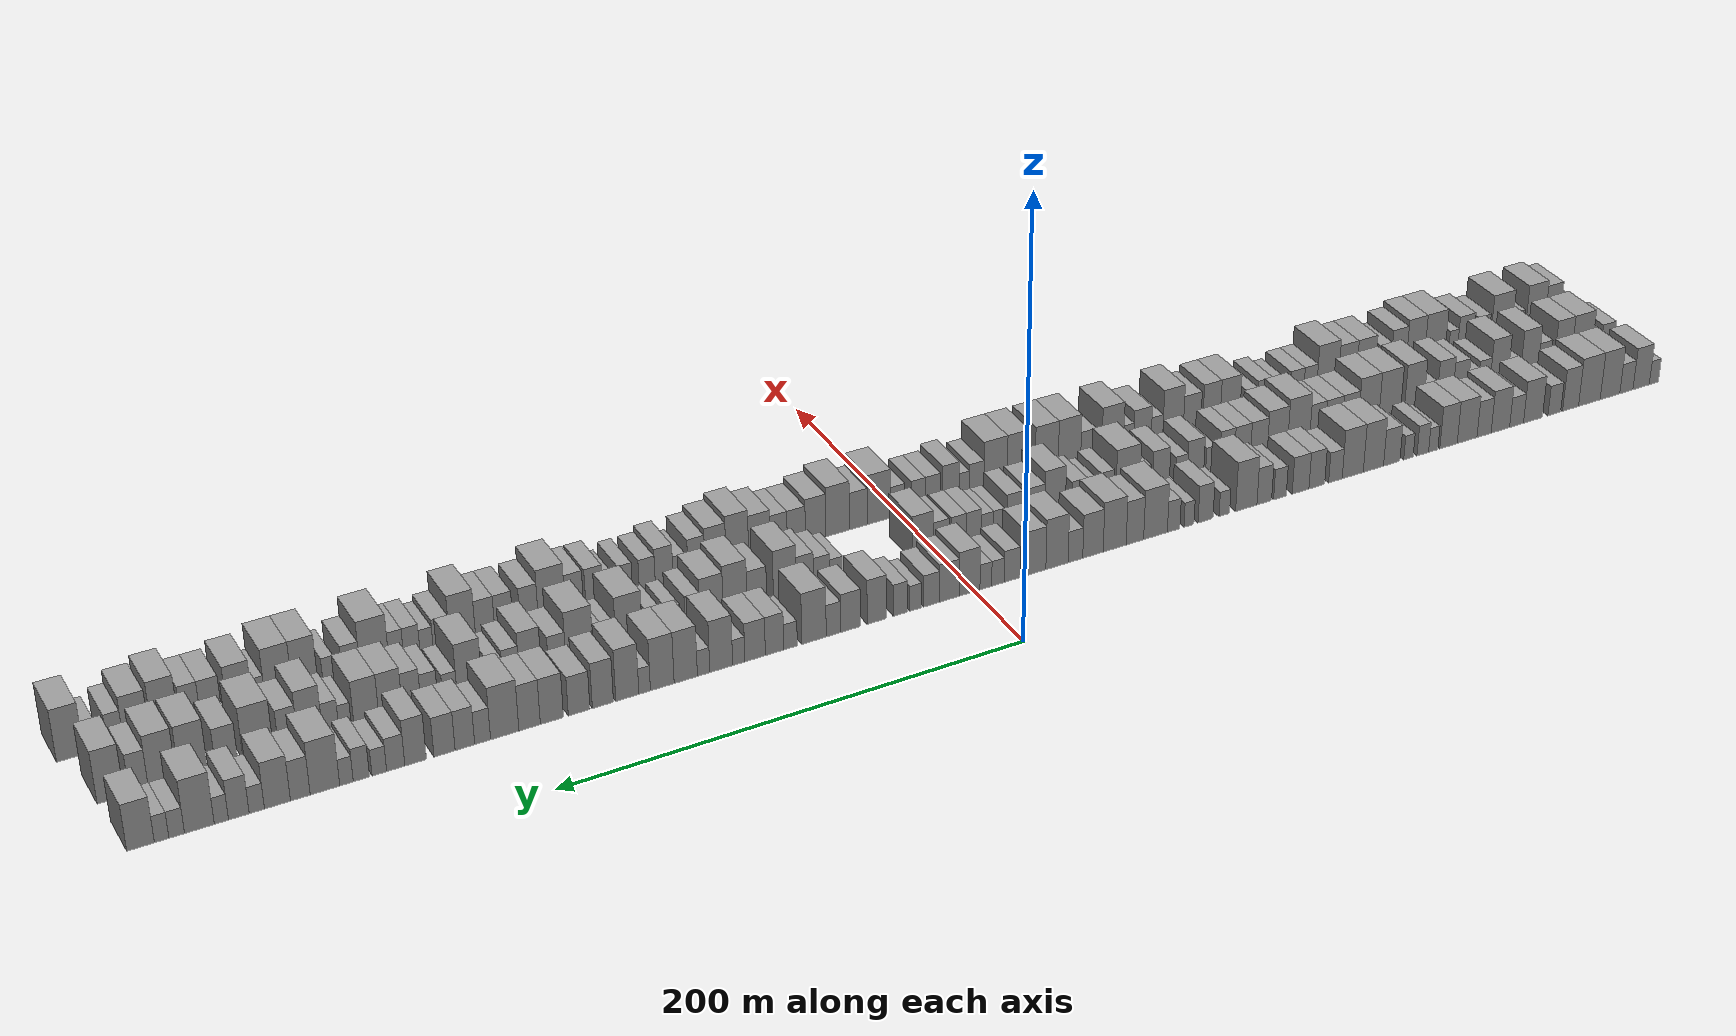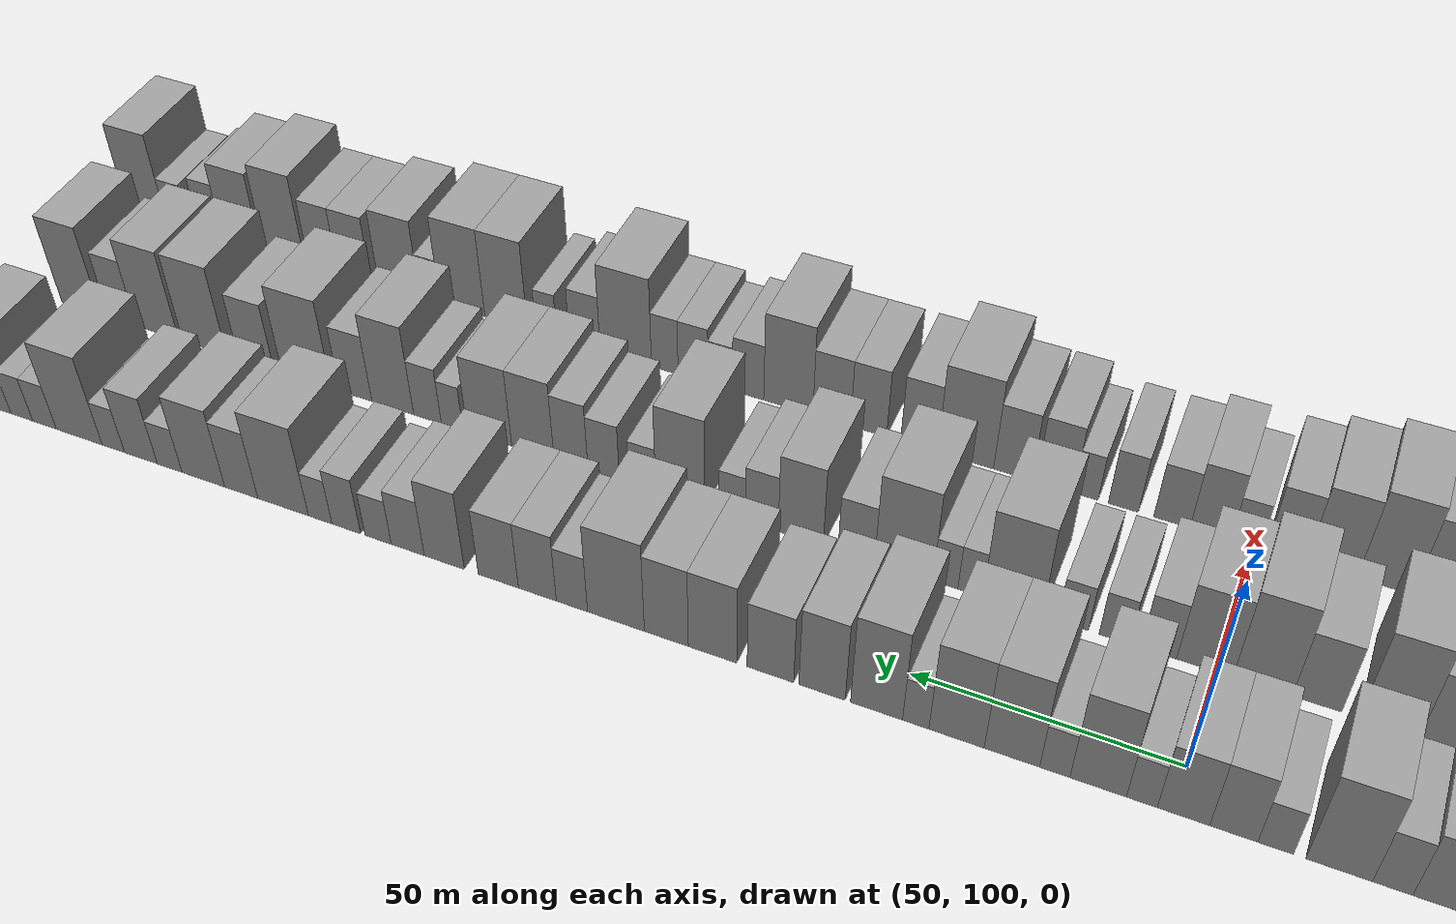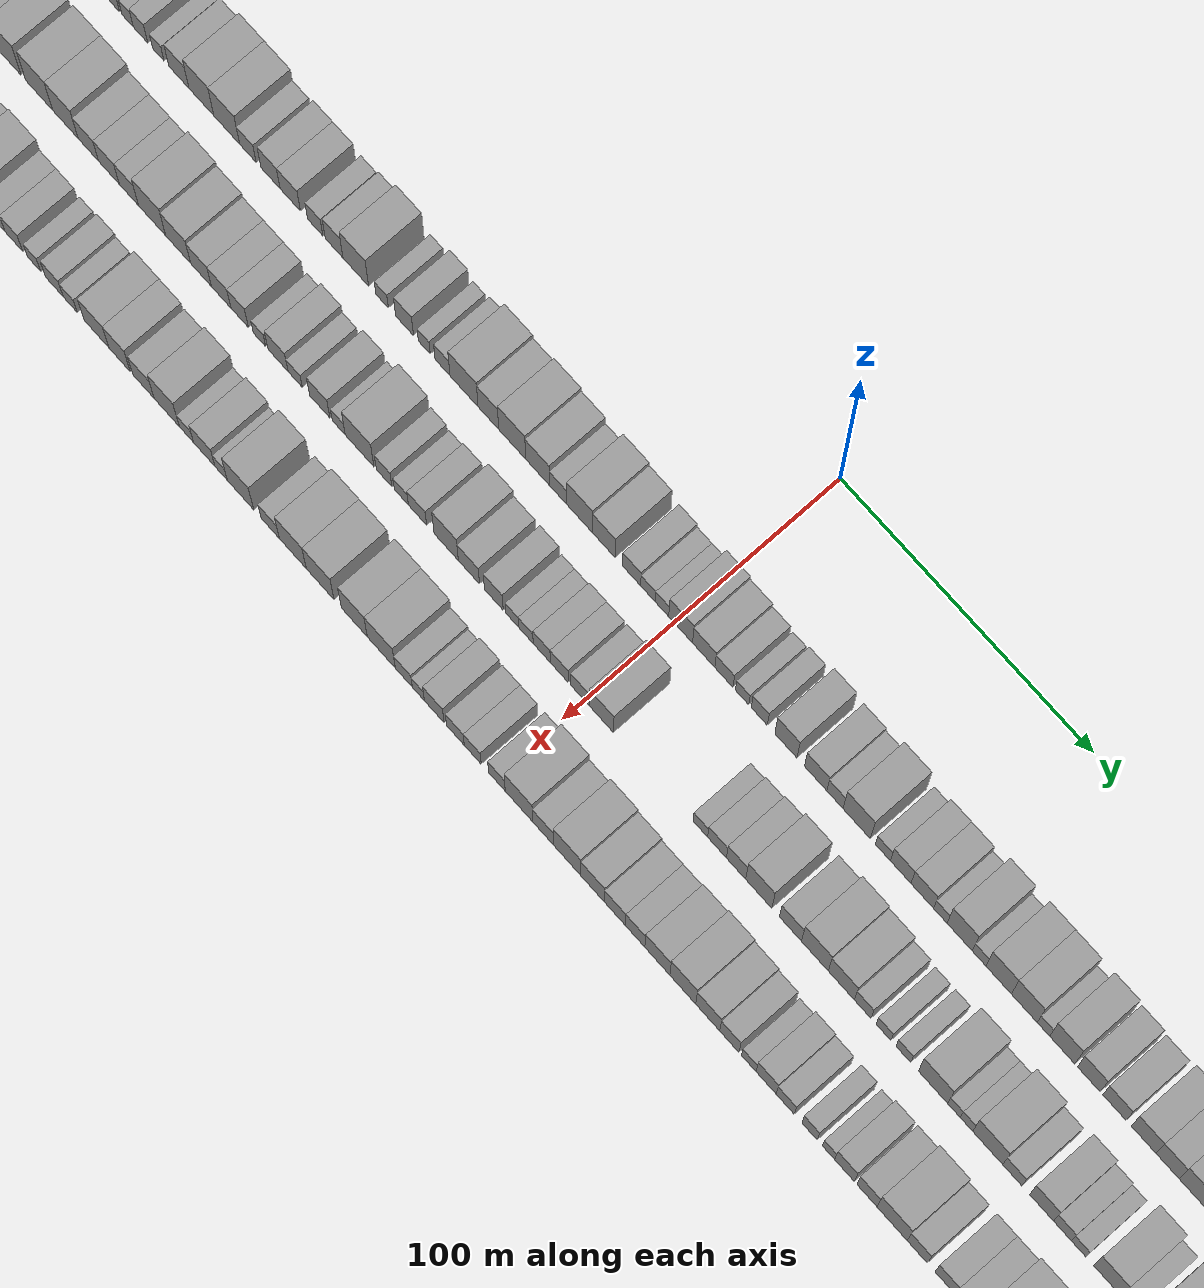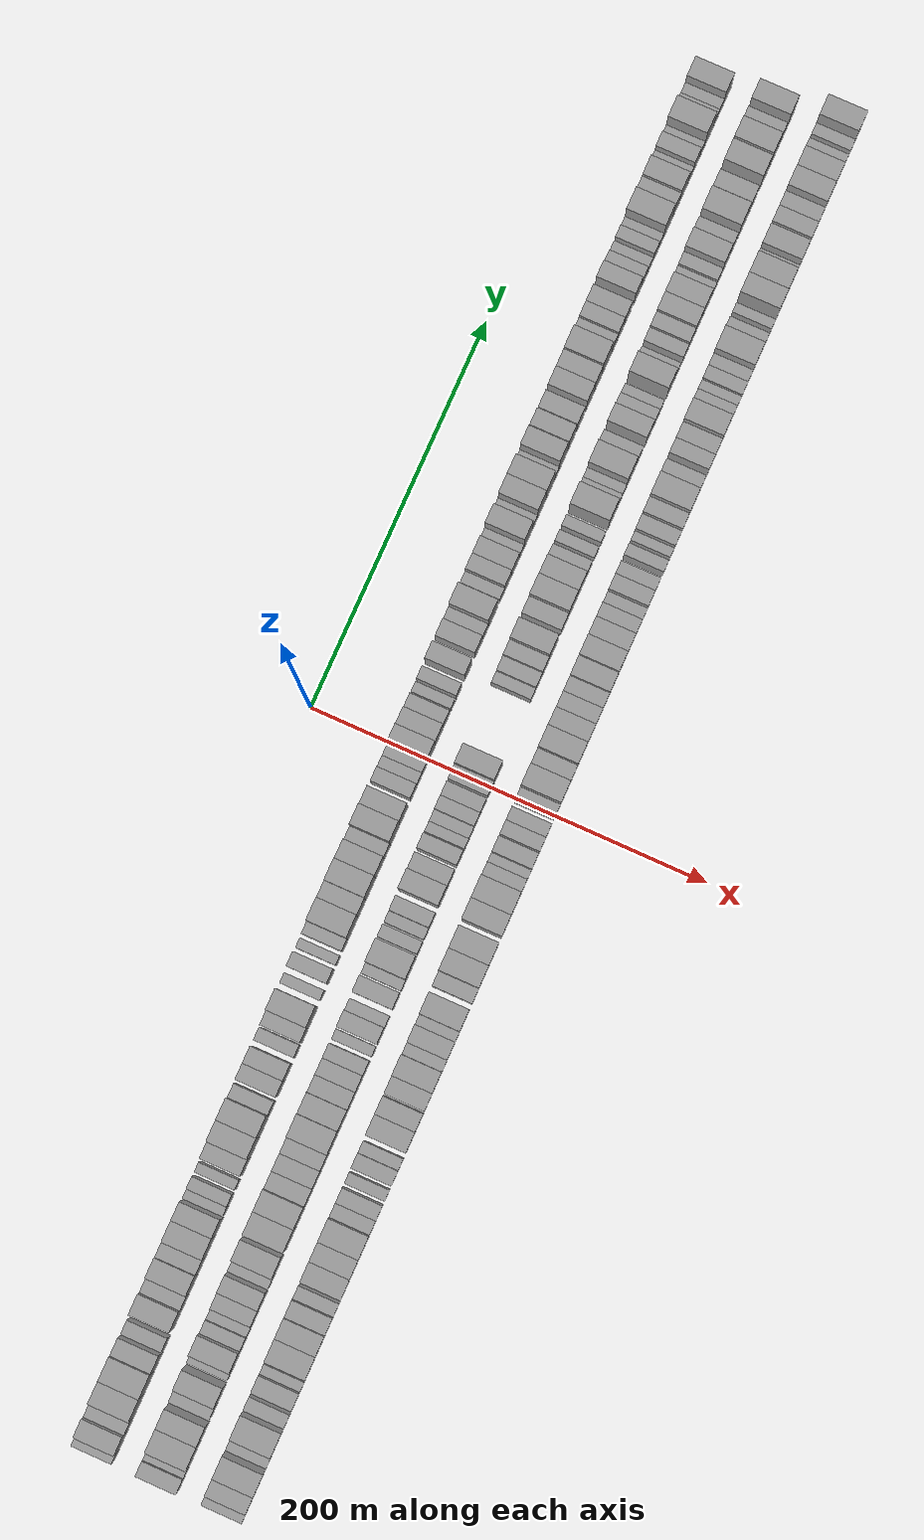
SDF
<sdf version="1.6">
 <world name="default">
  <scene>
   <sky><clouds><speed>12</speed></clouds></sky>
   <ambient>0.4 0.4 0.4 1</ambient>
   <background>0.7 0.7 0.7 1</background>
   <shadows>1</shadows>
  </scene>
  <gravity>0 0 -9.8066</gravity>
  <magnetic_field>6e-06 2.3e-05 -4.2e-05</magnetic_field>
  <physics default="0" name="default_physics" type="ode">
   <ode>
    <solver>
     <type>quick</type>
     <iters>10</iters>
     <sor>1.0</sor>
     <use_dynamic_moi_rescaling>0</use_dynamic_moi_rescaling>
    </solver>
    <constraints>
     <cfm>0</cfm>
     <erp>0.2</erp>
     <contact_max_correcting_vel>100</contact_max_correcting_vel>
     <contact_surface_layer>0.001</contact_surface_layer>
    </constraints>
   </ode>
   <max_step_size>0.004</max_step_size>
   <real_time_factor>1</real_time_factor>
   <real_time_update_rate>250</real_time_update_rate>
  </physics>
  <light name="sun" type="directional">
   <pose>0 0 10 0 0 0</pose>
   <diffuse>0.8 0.8 0.8 1</diffuse>
   <specular>0.2 0.2 0.2 1</specular>
   <attenuation>
    <range>1000</range>
    <constant>0.9</constant>
    <linear>0.01</linear>
    <quadratic>0.001</quadratic>
   </attenuation>
   <direction>-0.5 0.1 -0.9</direction>
  </light>
  <model name="building_1">
   <static>1</static>
   <pose>50.0000 -345.4279 0 0.000000 0.000000 0.000000</pose>
   <link name="link">
    <pose>0 0 6.00 0 0 0</pose>
    <collision name="collision"><geometry><box><size>20.0000 5.1441 12.0000</size></box></geometry></collision>
    <visual name="visual">
     <cast_shadows>0</cast_shadows>
     <geometry><box><size>20.0000 5.1441 12.0000</size></box></geometry>
     <material>
      <script>
       <uri>model://grey_wall/materials/scripts</uri>
       <uri>model://grey_wall/materials/textures</uri>
       <name>vrc/grey_wall</name>
      </script>
     </material>
    </visual>
   </link>
  </model>
  <model name="building_2">
   <static>1</static>
   <pose>50.0000 -338.2973 0 0.000000 0.000000 0.000000</pose>
   <link name="link">
    <pose>0 0 10.50 0 0 0</pose>
    <collision name="collision"><geometry><box><size>20.0000 9.1171 21.0000</size></box></geometry></collision>
    <visual name="visual">
     <cast_shadows>0</cast_shadows>
     <geometry><box><size>20.0000 9.1171 21.0000</size></box></geometry>
     <material>
      <script>
       <uri>model://grey_wall/materials/scripts</uri>
       <uri>model://grey_wall/materials/textures</uri>
       <name>vrc/grey_wall</name>
      </script>
     </material>
    </visual>
   </link>
  </model>
  <model name="building_3">
   <static>1</static>
   <pose>50.0000 -330.0822 0 0.000000 0.000000 0.000000</pose>
   <link name="link">
    <pose>0 0 7.50 0 0 0</pose>
    <collision name="collision"><geometry><box><size>20.0000 7.3132 15.0000</size></box></geometry></collision>
    <visual name="visual">
     <cast_shadows>0</cast_shadows>
     <geometry><box><size>20.0000 7.3132 15.0000</size></box></geometry>
     <material>
      <script>
       <uri>model://grey_wall/materials/scripts</uri>
       <uri>model://grey_wall/materials/textures</uri>
       <name>vrc/grey_wall</name>
      </script>
     </material>
    </visual>
   </link>
  </model>
  <model name="building_4">
   <static>1</static>
   <pose>50.0000 -320.9923 0 0.000000 0.000000 0.000000</pose>
   <link name="link">
    <pose>0 0 12.00 0 0 0</pose>
    <collision name="collision"><geometry><box><size>20.0000 10.8666 24.0000</size></box></geometry></collision>
    <visual name="visual">
     <cast_shadows>0</cast_shadows>
     <geometry><box><size>20.0000 10.8666 24.0000</size></box></geometry>
     <material>
      <script>
       <uri>model://grey_wall/materials/scripts</uri>
       <uri>model://grey_wall/materials/textures</uri>
       <name>vrc/grey_wall</name>
      </script>
     </material>
    </visual>
   </link>
  </model>
  <model name="building_5">
   <static>1</static>
   <pose>50.0000 -309.6062 0 0.000000 0.000000 0.000000</pose>
   <link name="link">
    <pose>0 0 12.00 0 0 0</pose>
    <collision name="collision"><geometry><box><size>20.0000 11.9056 24.0000</size></box></geometry></collision>
    <visual name="visual">
     <cast_shadows>0</cast_shadows>
     <geometry><box><size>20.0000 11.9056 24.0000</size></box></geometry>
     <material>
      <script>
       <uri>model://grey_wall/materials/scripts</uri>
       <uri>model://grey_wall/materials/textures</uri>
       <name>vrc/grey_wall</name>
      </script>
     </material>
    </visual>
   </link>
  </model>
  <model name="building_6">
   <static>1</static>
   <pose>50.0000 -299.2852 0 0.000000 0.000000 0.000000</pose>
   <link name="link">
    <pose>0 0 10.50 0 0 0</pose>
    <collision name="collision"><geometry><box><size>20.0000 8.7364 21.0000</size></box></geometry></collision>
    <visual name="visual">
     <cast_shadows>0</cast_shadows>
     <geometry><box><size>20.0000 8.7364 21.0000</size></box></geometry>
     <material>
      <script>
       <uri>model://grey_wall/materials/scripts</uri>
       <uri>model://grey_wall/materials/textures</uri>
       <name>vrc/grey_wall</name>
      </script>
     </material>
    </visual>
   </link>
  </model>
  <model name="building_7">
   <static>1</static>
   <pose>50.0000 -290.4478 0 0.000000 0.000000 0.000000</pose>
   <link name="link">
    <pose>0 0 7.50 0 0 0</pose>
    <collision name="collision"><geometry><box><size>20.0000 6.9384 15.0000</size></box></geometry></collision>
    <visual name="visual">
     <cast_shadows>0</cast_shadows>
     <geometry><box><size>20.0000 6.9384 15.0000</size></box></geometry>
     <material>
      <script>
       <uri>model://grey_wall/materials/scripts</uri>
       <uri>model://grey_wall/materials/textures</uri>
       <name>vrc/grey_wall</name>
      </script>
     </material>
    </visual>
   </link>
  </model>
  <model name="building_8">
   <static>1</static>
   <pose>50.0000 -278.8510 0 0.000000 0.000000 0.000000</pose>
   <link name="link">
    <pose>0 0 10.50 0 0 0</pose>
    <collision name="collision"><geometry><box><size>20.0000 10.2552 21.0000</size></box></geometry></collision>
    <visual name="visual">
     <cast_shadows>0</cast_shadows>
     <geometry><box><size>20.0000 10.2552 21.0000</size></box></geometry>
     <material>
      <script>
       <uri>model://grey_wall/materials/scripts</uri>
       <uri>model://grey_wall/materials/textures</uri>
       <name>vrc/grey_wall</name>
      </script>
     </material>
    </visual>
   </link>
  </model>
  <model name="building_9">
   <static>1</static>
   <pose>50.0000 -269.9844 0 0.000000 0.000000 0.000000</pose>
   <link name="link">
    <pose>0 0 7.50 0 0 0</pose>
    <collision name="collision"><geometry><box><size>20.0000 7.4780 15.0000</size></box></geometry></collision>
    <visual name="visual">
     <cast_shadows>0</cast_shadows>
     <geometry><box><size>20.0000 7.4780 15.0000</size></box></geometry>
     <material>
      <script>
       <uri>model://grey_wall/materials/scripts</uri>
       <uri>model://grey_wall/materials/textures</uri>
       <name>vrc/grey_wall</name>
      </script>
     </material>
    </visual>
   </link>
  </model>
  <model name="building_10">
   <static>1</static>
   <pose>50.0000 -261.2865 0 0.000000 0.000000 0.000000</pose>
   <link name="link">
    <pose>0 0 10.50 0 0 0</pose>
    <collision name="collision"><geometry><box><size>20.0000 9.9178 21.0000</size></box></geometry></collision>
    <visual name="visual">
     <cast_shadows>0</cast_shadows>
     <geometry><box><size>20.0000 9.9178 21.0000</size></box></geometry>
     <material>
      <script>
       <uri>model://grey_wall/materials/scripts</uri>
       <uri>model://grey_wall/materials/textures</uri>
       <name>vrc/grey_wall</name>
      </script>
     </material>
    </visual>
   </link>
  </model>
  <model name="building_11">
   <static>1</static>
   <pose>50.0000 -252.5657 0 0.000000 0.000000 0.000000</pose>
   <link name="link">
    <pose>0 0 9.00 0 0 0</pose>
    <collision name="collision"><geometry><box><size>20.0000 7.5238 18.0000</size></box></geometry></collision>
    <visual name="visual">
     <cast_shadows>0</cast_shadows>
     <geometry><box><size>20.0000 7.5238 18.0000</size></box></geometry>
     <material>
      <script>
       <uri>model://grey_wall/materials/scripts</uri>
       <uri>model://grey_wall/materials/textures</uri>
       <name>vrc/grey_wall</name>
      </script>
     </material>
    </visual>
   </link>
  </model>
  <model name="building_12">
   <static>1</static>
   <pose>50.0000 -243.5626 0 0.000000 0.000000 0.000000</pose>
   <link name="link">
    <pose>0 0 10.50 0 0 0</pose>
    <collision name="collision"><geometry><box><size>20.0000 10.4824 21.0000</size></box></geometry></collision>
    <visual name="visual">
     <cast_shadows>0</cast_shadows>
     <geometry><box><size>20.0000 10.4824 21.0000</size></box></geometry>
     <material>
      <script>
       <uri>model://grey_wall/materials/scripts</uri>
       <uri>model://grey_wall/materials/textures</uri>
       <name>vrc/grey_wall</name>
      </script>
     </material>
    </visual>
   </link>
  </model>
  <model name="building_13">
   <static>1</static>
   <pose>50.0000 -233.7275 0 0.000000 0.000000 0.000000</pose>
   <link name="link">
    <pose>0 0 10.50 0 0 0</pose>
    <collision name="collision"><geometry><box><size>20.0000 9.1879 21.0000</size></box></geometry></collision>
    <visual name="visual">
     <cast_shadows>0</cast_shadows>
     <geometry><box><size>20.0000 9.1879 21.0000</size></box></geometry>
     <material>
      <script>
       <uri>model://grey_wall/materials/scripts</uri>
       <uri>model://grey_wall/materials/textures</uri>
       <name>vrc/grey_wall</name>
      </script>
     </material>
    </visual>
   </link>
  </model>
  <model name="building_14">
   <static>1</static>
   <pose>50.0000 -225.6845 0 0.000000 0.000000 0.000000</pose>
   <link name="link">
    <pose>0 0 6.00 0 0 0</pose>
    <collision name="collision"><geometry><box><size>20.0000 4.8980 12.0000</size></box></geometry></collision>
    <visual name="visual">
     <cast_shadows>0</cast_shadows>
     <geometry><box><size>20.0000 4.8980 12.0000</size></box></geometry>
     <material>
      <script>
       <uri>model://grey_wall/materials/scripts</uri>
       <uri>model://grey_wall/materials/textures</uri>
       <name>vrc/grey_wall</name>
      </script>
     </material>
    </visual>
   </link>
  </model>
  <model name="building_15">
   <static>1</static>
   <pose>50.0000 -220.1928 0 0.000000 0.000000 0.000000</pose>
   <link name="link">
    <pose>0 0 7.50 0 0 0</pose>
    <collision name="collision"><geometry><box><size>20.0000 6.0856 15.0000</size></box></geometry></collision>
    <visual name="visual">
     <cast_shadows>0</cast_shadows>
     <geometry><box><size>20.0000 6.0856 15.0000</size></box></geometry>
     <material>
      <script>
       <uri>model://grey_wall/materials/scripts</uri>
       <uri>model://grey_wall/materials/textures</uri>
       <name>vrc/grey_wall</name>
      </script>
     </material>
    </visual>
   </link>
  </model>
  <model name="building_16">
   <static>1</static>
   <pose>50.0000 -212.7110 0 0.000000 0.000000 0.000000</pose>
   <link name="link">
    <pose>0 0 6.00 0 0 0</pose>
    <collision name="collision"><geometry><box><size>20.0000 4.8779 12.0000</size></box></geometry></collision>
    <visual name="visual">
     <cast_shadows>0</cast_shadows>
     <geometry><box><size>20.0000 4.8779 12.0000</size></box></geometry>
     <material>
      <script>
       <uri>model://grey_wall/materials/scripts</uri>
       <uri>model://grey_wall/materials/textures</uri>
       <name>vrc/grey_wall</name>
      </script>
     </material>
    </visual>
   </link>
  </model>
  <model name="building_17">
   <static>1</static>
   <pose>50.0000 -204.0332 0 0.000000 0.000000 0.000000</pose>
   <link name="link">
    <pose>0 0 9.00 0 0 0</pose>
    <collision name="collision"><geometry><box><size>20.0000 8.4778 18.0000</size></box></geometry></collision>
    <visual name="visual">
     <cast_shadows>0</cast_shadows>
     <geometry><box><size>20.0000 8.4778 18.0000</size></box></geometry>
     <material>
      <script>
       <uri>model://grey_wall/materials/scripts</uri>
       <uri>model://grey_wall/materials/textures</uri>
       <name>vrc/grey_wall</name>
      </script>
     </material>
    </visual>
   </link>
  </model>
  <model name="building_18">
   <static>1</static>
   <pose>50.0000 -194.5621 0 0.000000 0.000000 0.000000</pose>
   <link name="link">
    <pose>0 0 12.00 0 0 0</pose>
    <collision name="collision"><geometry><box><size>20.0000 10.4643 24.0000</size></box></geometry></collision>
    <visual name="visual">
     <cast_shadows>0</cast_shadows>
     <geometry><box><size>20.0000 10.4643 24.0000</size></box></geometry>
     <material>
      <script>
       <uri>model://grey_wall/materials/scripts</uri>
       <uri>model://grey_wall/materials/textures</uri>
       <name>vrc/grey_wall</name>
      </script>
     </material>
    </visual>
   </link>
  </model>
  <model name="building_19">
   <static>1</static>
   <pose>50.0000 -183.9129 0 0.000000 0.000000 0.000000</pose>
   <link name="link">
    <pose>0 0 12.00 0 0 0</pose>
    <collision name="collision"><geometry><box><size>20.0000 10.8343 24.0000</size></box></geometry></collision>
    <visual name="visual">
     <cast_shadows>0</cast_shadows>
     <geometry><box><size>20.0000 10.8343 24.0000</size></box></geometry>
     <material>
      <script>
       <uri>model://grey_wall/materials/scripts</uri>
       <uri>model://grey_wall/materials/textures</uri>
       <name>vrc/grey_wall</name>
      </script>
     </material>
    </visual>
   </link>
  </model>
  <model name="building_20">
   <static>1</static>
   <pose>50.0000 -175.0289 0 0.000000 0.000000 0.000000</pose>
   <link name="link">
    <pose>0 0 7.50 0 0 0</pose>
    <collision name="collision"><geometry><box><size>20.0000 6.9336 15.0000</size></box></geometry></collision>
    <visual name="visual">
     <cast_shadows>0</cast_shadows>
     <geometry><box><size>20.0000 6.9336 15.0000</size></box></geometry>
     <material>
      <script>
       <uri>model://grey_wall/materials/scripts</uri>
       <uri>model://grey_wall/materials/textures</uri>
       <name>vrc/grey_wall</name>
      </script>
     </material>
    </visual>
   </link>
  </model>
  <model name="building_21">
   <static>1</static>
   <pose>50.0000 -165.5699 0 0.000000 0.000000 0.000000</pose>
   <link name="link">
    <pose>0 0 9.00 0 0 0</pose>
    <collision name="collision"><geometry><box><size>20.0000 7.9845 18.0000</size></box></geometry></collision>
    <visual name="visual">
     <cast_shadows>0</cast_shadows>
     <geometry><box><size>20.0000 7.9845 18.0000</size></box></geometry>
     <material>
      <script>
       <uri>model://grey_wall/materials/scripts</uri>
       <uri>model://grey_wall/materials/textures</uri>
       <name>vrc/grey_wall</name>
      </script>
     </material>
    </visual>
   </link>
  </model>
  <model name="building_22">
   <static>1</static>
   <pose>50.0000 -157.3388 0 0.000000 0.000000 0.000000</pose>
   <link name="link">
    <pose>0 0 9.00 0 0 0</pose>
    <collision name="collision"><geometry><box><size>20.0000 8.4777 18.0000</size></box></geometry></collision>
    <visual name="visual">
     <cast_shadows>0</cast_shadows>
     <geometry><box><size>20.0000 8.4777 18.0000</size></box></geometry>
     <material>
      <script>
       <uri>model://grey_wall/materials/scripts</uri>
       <uri>model://grey_wall/materials/textures</uri>
       <name>vrc/grey_wall</name>
      </script>
     </material>
    </visual>
   </link>
  </model>
  <model name="building_23">
   <static>1</static>
   <pose>50.0000 -146.9242 0 0.000000 0.000000 0.000000</pose>
   <link name="link">
    <pose>0 0 7.50 0 0 0</pose>
    <collision name="collision"><geometry><box><size>20.0000 6.3514 15.0000</size></box></geometry></collision>
    <visual name="visual">
     <cast_shadows>0</cast_shadows>
     <geometry><box><size>20.0000 6.3514 15.0000</size></box></geometry>
     <material>
      <script>
       <uri>model://grey_wall/materials/scripts</uri>
       <uri>model://grey_wall/materials/textures</uri>
       <name>vrc/grey_wall</name>
      </script>
     </material>
    </visual>
   </link>
  </model>
  <model name="building_24">
   <static>1</static>
   <pose>50.0000 -139.0835 0 0.000000 0.000000 0.000000</pose>
   <link name="link">
    <pose>0 0 9.00 0 0 0</pose>
    <collision name="collision"><geometry><box><size>20.0000 7.3302 18.0000</size></box></geometry></collision>
    <visual name="visual">
     <cast_shadows>0</cast_shadows>
     <geometry><box><size>20.0000 7.3302 18.0000</size></box></geometry>
     <material>
      <script>
       <uri>model://grey_wall/materials/scripts</uri>
       <uri>model://grey_wall/materials/textures</uri>
       <name>vrc/grey_wall</name>
      </script>
     </material>
    </visual>
   </link>
  </model>
  <model name="building_25">
   <static>1</static>
   <pose>50.0000 -130.1029 0 0.000000 0.000000 0.000000</pose>
   <link name="link">
    <pose>0 0 12.00 0 0 0</pose>
    <collision name="collision"><geometry><box><size>20.0000 10.6309 24.0000</size></box></geometry></collision>
    <visual name="visual">
     <cast_shadows>0</cast_shadows>
     <geometry><box><size>20.0000 10.6309 24.0000</size></box></geometry>
     <material>
      <script>
       <uri>model://grey_wall/materials/scripts</uri>
       <uri>model://grey_wall/materials/textures</uri>
       <name>vrc/grey_wall</name>
      </script>
     </material>
    </visual>
   </link>
  </model>
  <model name="building_26">
   <static>1</static>
   <pose>50.0000 -119.1992 0 0.000000 0.000000 0.000000</pose>
   <link name="link">
    <pose>0 0 6.00 0 0 0</pose>
    <collision name="collision"><geometry><box><size>20.0000 5.1765 12.0000</size></box></geometry></collision>
    <visual name="visual">
     <cast_shadows>0</cast_shadows>
     <geometry><box><size>20.0000 5.1765 12.0000</size></box></geometry>
     <material>
      <script>
       <uri>model://grey_wall/materials/scripts</uri>
       <uri>model://grey_wall/materials/textures</uri>
       <name>vrc/grey_wall</name>
      </script>
     </material>
    </visual>
   </link>
  </model>
  <model name="building_27">
   <static>1</static>
   <pose>50.0000 -109.9316 0 0.000000 0.000000 0.000000</pose>
   <link name="link">
    <pose>0 0 9.00 0 0 0</pose>
    <collision name="collision"><geometry><box><size>20.0000 7.3586 18.0000</size></box></geometry></collision>
    <visual name="visual">
     <cast_shadows>0</cast_shadows>
     <geometry><box><size>20.0000 7.3586 18.0000</size></box></geometry>
     <material>
      <script>
       <uri>model://grey_wall/materials/scripts</uri>
       <uri>model://grey_wall/materials/textures</uri>
       <name>vrc/grey_wall</name>
      </script>
     </material>
    </visual>
   </link>
  </model>
  <model name="building_28">
   <static>1</static>
   <pose>50.0000 -101.8058 0 0.000000 0.000000 0.000000</pose>
   <link name="link">
    <pose>0 0 6.00 0 0 0</pose>
    <collision name="collision"><geometry><box><size>20.0000 4.8930 12.0000</size></box></geometry></collision>
    <visual name="visual">
     <cast_shadows>0</cast_shadows>
     <geometry><box><size>20.0000 4.8930 12.0000</size></box></geometry>
     <material>
      <script>
       <uri>model://grey_wall/materials/scripts</uri>
       <uri>model://grey_wall/materials/textures</uri>
       <name>vrc/grey_wall</name>
      </script>
     </material>
    </visual>
   </link>
  </model>
  <model name="building_29">
   <static>1</static>
   <pose>50.0000 -94.3049 0 0.000000 0.000000 0.000000</pose>
   <link name="link">
    <pose>0 0 7.50 0 0 0</pose>
    <collision name="collision"><geometry><box><size>20.0000 6.1090 15.0000</size></box></geometry></collision>
    <visual name="visual">
     <cast_shadows>0</cast_shadows>
     <geometry><box><size>20.0000 6.1090 15.0000</size></box></geometry>
     <material>
      <script>
       <uri>model://grey_wall/materials/scripts</uri>
       <uri>model://grey_wall/materials/textures</uri>
       <name>vrc/grey_wall</name>
      </script>
     </material>
    </visual>
   </link>
  </model>
  <model name="building_30">
   <static>1</static>
   <pose>50.0000 -85.5007 0 0.000000 0.000000 0.000000</pose>
   <link name="link">
    <pose>0 0 12.00 0 0 0</pose>
    <collision name="collision"><geometry><box><size>20.0000 11.4992 24.0000</size></box></geometry></collision>
    <visual name="visual">
     <cast_shadows>0</cast_shadows>
     <geometry><box><size>20.0000 11.4992 24.0000</size></box></geometry>
     <material>
      <script>
       <uri>model://grey_wall/materials/scripts</uri>
       <uri>model://grey_wall/materials/textures</uri>
       <name>vrc/grey_wall</name>
      </script>
     </material>
    </visual>
   </link>
  </model>
  <model name="building_31">
   <static>1</static>
   <pose>50.0000 -75.5200 0 0.000000 0.000000 0.000000</pose>
   <link name="link">
    <pose>0 0 10.50 0 0 0</pose>
    <collision name="collision"><geometry><box><size>20.0000 8.4622 21.0000</size></box></geometry></collision>
    <visual name="visual">
     <cast_shadows>0</cast_shadows>
     <geometry><box><size>20.0000 8.4622 21.0000</size></box></geometry>
     <material>
      <script>
       <uri>model://grey_wall/materials/scripts</uri>
       <uri>model://grey_wall/materials/textures</uri>
       <name>vrc/grey_wall</name>
      </script>
     </material>
    </visual>
   </link>
  </model>
  <model name="building_32">
   <static>1</static>
   <pose>50.0000 -65.7874 0 0.000000 0.000000 0.000000</pose>
   <link name="link">
    <pose>0 0 12.00 0 0 0</pose>
    <collision name="collision"><geometry><box><size>20.0000 11.0031 24.0000</size></box></geometry></collision>
    <visual name="visual">
     <cast_shadows>0</cast_shadows>
     <geometry><box><size>20.0000 11.0031 24.0000</size></box></geometry>
     <material>
      <script>
       <uri>model://grey_wall/materials/scripts</uri>
       <uri>model://grey_wall/materials/textures</uri>
       <name>vrc/grey_wall</name>
      </script>
     </material>
    </visual>
   </link>
  </model>
  <model name="building_33">
   <static>1</static>
   <pose>50.0000 -55.4217 0 0.000000 0.000000 0.000000</pose>
   <link name="link">
    <pose>0 0 10.50 0 0 0</pose>
    <collision name="collision"><geometry><box><size>20.0000 9.7284 21.0000</size></box></geometry></collision>
    <visual name="visual">
     <cast_shadows>0</cast_shadows>
     <geometry><box><size>20.0000 9.7284 21.0000</size></box></geometry>
     <material>
      <script>
       <uri>model://grey_wall/materials/scripts</uri>
       <uri>model://grey_wall/materials/textures</uri>
       <name>vrc/grey_wall</name>
      </script>
     </material>
    </visual>
   </link>
  </model>
  <model name="building_34">
   <static>1</static>
   <pose>50.0000 -47.0706 0 0.000000 0.000000 0.000000</pose>
   <link name="link">
    <pose>0 0 7.50 0 0 0</pose>
    <collision name="collision"><geometry><box><size>20.0000 6.9736 15.0000</size></box></geometry></collision>
    <visual name="visual">
     <cast_shadows>0</cast_shadows>
     <geometry><box><size>20.0000 6.9736 15.0000</size></box></geometry>
     <material>
      <script>
       <uri>model://grey_wall/materials/scripts</uri>
       <uri>model://grey_wall/materials/textures</uri>
       <name>vrc/grey_wall</name>
      </script>
     </material>
    </visual>
   </link>
  </model>
  <model name="building_35">
   <static>1</static>
   <pose>50.0000 -38.3505 0 0.000000 0.000000 0.000000</pose>
   <link name="link">
    <pose>0 0 12.00 0 0 0</pose>
    <collision name="collision"><geometry><box><size>20.0000 10.4667 24.0000</size></box></geometry></collision>
    <visual name="visual">
     <cast_shadows>0</cast_shadows>
     <geometry><box><size>20.0000 10.4667 24.0000</size></box></geometry>
     <material>
      <script>
       <uri>model://grey_wall/materials/scripts</uri>
       <uri>model://grey_wall/materials/textures</uri>
       <name>vrc/grey_wall</name>
      </script>
     </material>
    </visual>
   </link>
  </model>
  <model name="building_36">
   <static>1</static>
   <pose>50.0000 -28.5436 0 0.000000 0.000000 0.000000</pose>
   <link name="link">
    <pose>0 0 10.50 0 0 0</pose>
    <collision name="collision"><geometry><box><size>20.0000 9.1469 21.0000</size></box></geometry></collision>
    <visual name="visual">
     <cast_shadows>0</cast_shadows>
     <geometry><box><size>20.0000 9.1469 21.0000</size></box></geometry>
     <material>
      <script>
       <uri>model://grey_wall/materials/scripts</uri>
       <uri>model://grey_wall/materials/textures</uri>
       <name>vrc/grey_wall</name>
      </script>
     </material>
    </visual>
   </link>
  </model>
  <model name="building_37">
   <static>1</static>
   <pose>50.0000 -17.3323 0 0.000000 0.000000 0.000000</pose>
   <link name="link">
    <pose>0 0 7.50 0 0 0</pose>
    <collision name="collision"><geometry><box><size>20.0000 7.2758 15.0000</size></box></geometry></collision>
    <visual name="visual">
     <cast_shadows>0</cast_shadows>
     <geometry><box><size>20.0000 7.2758 15.0000</size></box></geometry>
     <material>
      <script>
       <uri>model://grey_wall/materials/scripts</uri>
       <uri>model://grey_wall/materials/textures</uri>
       <name>vrc/grey_wall</name>
      </script>
     </material>
    </visual>
   </link>
  </model>
  <model name="building_38">
   <static>1</static>
   <pose>50.0000 -10.7607 0 0.000000 0.000000 0.000000</pose>
   <link name="link">
    <pose>0 0 6.00 0 0 0</pose>
    <collision name="collision"><geometry><box><size>20.0000 5.8672 12.0000</size></box></geometry></collision>
    <visual name="visual">
     <cast_shadows>0</cast_shadows>
     <geometry><box><size>20.0000 5.8672 12.0000</size></box></geometry>
     <material>
      <script>
       <uri>model://grey_wall/materials/scripts</uri>
       <uri>model://grey_wall/materials/textures</uri>
       <name>vrc/grey_wall</name>
      </script>
     </material>
    </visual>
   </link>
  </model>
  <model name="building_39">
   <static>1</static>
   <pose>50.0000 -5.1017 0 0.000000 0.000000 0.000000</pose>
   <link name="link">
    <pose>0 0 6.00 0 0 0</pose>
    <collision name="collision"><geometry><box><size>20.0000 5.4508 12.0000</size></box></geometry></collision>
    <visual name="visual">
     <cast_shadows>0</cast_shadows>
     <geometry><box><size>20.0000 5.4508 12.0000</size></box></geometry>
     <material>
      <script>
       <uri>model://grey_wall/materials/scripts</uri>
       <uri>model://grey_wall/materials/textures</uri>
       <name>vrc/grey_wall</name>
      </script>
     </material>
    </visual>
   </link>
  </model>
  <model name="building_40">
   <static>1</static>
   <pose>50.0000 2.4030 0 0.000000 0.000000 0.000000</pose>
   <link name="link">
    <pose>0 0 10.50 0 0 0</pose>
    <collision name="collision"><geometry><box><size>20.0000 9.5587 21.0000</size></box></geometry></collision>
    <visual name="visual">
     <cast_shadows>0</cast_shadows>
     <geometry><box><size>20.0000 9.5587 21.0000</size></box></geometry>
     <material>
      <script>
       <uri>model://grey_wall/materials/scripts</uri>
       <uri>model://grey_wall/materials/textures</uri>
       <name>vrc/grey_wall</name>
      </script>
     </material>
    </visual>
   </link>
  </model>
  <model name="building_41">
   <static>1</static>
   <pose>50.0000 11.6549 0 0.000000 0.000000 0.000000</pose>
   <link name="link">
    <pose>0 0 9.00 0 0 0</pose>
    <collision name="collision"><geometry><box><size>20.0000 8.9450 18.0000</size></box></geometry></collision>
    <visual name="visual">
     <cast_shadows>0</cast_shadows>
     <geometry><box><size>20.0000 8.9450 18.0000</size></box></geometry>
     <material>
      <script>
       <uri>model://grey_wall/materials/scripts</uri>
       <uri>model://grey_wall/materials/textures</uri>
       <name>vrc/grey_wall</name>
      </script>
     </material>
    </visual>
   </link>
  </model>
  <model name="building_42">
   <static>1</static>
   <pose>50.0000 19.7521 0 0.000000 0.000000 0.000000</pose>
   <link name="link">
    <pose>0 0 7.50 0 0 0</pose>
    <collision name="collision"><geometry><box><size>20.0000 7.2494 15.0000</size></box></geometry></collision>
    <visual name="visual">
     <cast_shadows>0</cast_shadows>
     <geometry><box><size>20.0000 7.2494 15.0000</size></box></geometry>
     <material>
      <script>
       <uri>model://grey_wall/materials/scripts</uri>
       <uri>model://grey_wall/materials/textures</uri>
       <name>vrc/grey_wall</name>
      </script>
     </material>
    </visual>
   </link>
  </model>
  <model name="building_43">
   <static>1</static>
   <pose>50.0000 27.0330 0 0.000000 0.000000 0.000000</pose>
   <link name="link">
    <pose>0 0 6.00 0 0 0</pose>
    <collision name="collision"><geometry><box><size>20.0000 5.3125 12.0000</size></box></geometry></collision>
    <visual name="visual">
     <cast_shadows>0</cast_shadows>
     <geometry><box><size>20.0000 5.3125 12.0000</size></box></geometry>
     <material>
      <script>
       <uri>model://grey_wall/materials/scripts</uri>
       <uri>model://grey_wall/materials/textures</uri>
       <name>vrc/grey_wall</name>
      </script>
     </material>
    </visual>
   </link>
  </model>
  <model name="building_44">
   <static>1</static>
   <pose>50.0000 33.8984 0 0.000000 0.000000 0.000000</pose>
   <link name="link">
    <pose>0 0 7.50 0 0 0</pose>
    <collision name="collision"><geometry><box><size>20.0000 6.4183 15.0000</size></box></geometry></collision>
    <visual name="visual">
     <cast_shadows>0</cast_shadows>
     <geometry><box><size>20.0000 6.4183 15.0000</size></box></geometry>
     <material>
      <script>
       <uri>model://grey_wall/materials/scripts</uri>
       <uri>model://grey_wall/materials/textures</uri>
       <name>vrc/grey_wall</name>
      </script>
     </material>
    </visual>
   </link>
  </model>
  <model name="building_45">
   <static>1</static>
   <pose>50.0000 44.5036 0 0.000000 0.000000 0.000000</pose>
   <link name="link">
    <pose>0 0 10.50 0 0 0</pose>
    <collision name="collision"><geometry><box><size>20.0000 8.7922 21.0000</size></box></geometry></collision>
    <visual name="visual">
     <cast_shadows>0</cast_shadows>
     <geometry><box><size>20.0000 8.7922 21.0000</size></box></geometry>
     <material>
      <script>
       <uri>model://grey_wall/materials/scripts</uri>
       <uri>model://grey_wall/materials/textures</uri>
       <name>vrc/grey_wall</name>
      </script>
     </material>
    </visual>
   </link>
  </model>
  <model name="building_46">
   <static>1</static>
   <pose>50.0000 56.3136 0 0.000000 0.000000 0.000000</pose>
   <link name="link">
    <pose>0 0 9.00 0 0 0</pose>
    <collision name="collision"><geometry><box><size>20.0000 8.8278 18.0000</size></box></geometry></collision>
    <visual name="visual">
     <cast_shadows>0</cast_shadows>
     <geometry><box><size>20.0000 8.8278 18.0000</size></box></geometry>
     <material>
      <script>
       <uri>model://grey_wall/materials/scripts</uri>
       <uri>model://grey_wall/materials/textures</uri>
       <name>vrc/grey_wall</name>
      </script>
     </material>
    </visual>
   </link>
  </model>
  <model name="building_47">
   <static>1</static>
   <pose>50.0000 63.9423 0 0.000000 0.000000 0.000000</pose>
   <link name="link">
    <pose>0 0 7.50 0 0 0</pose>
    <collision name="collision"><geometry><box><size>20.0000 6.4296 15.0000</size></box></geometry></collision>
    <visual name="visual">
     <cast_shadows>0</cast_shadows>
     <geometry><box><size>20.0000 6.4296 15.0000</size></box></geometry>
     <material>
      <script>
       <uri>model://grey_wall/materials/scripts</uri>
       <uri>model://grey_wall/materials/textures</uri>
       <name>vrc/grey_wall</name>
      </script>
     </material>
    </visual>
   </link>
  </model>
  <model name="building_48">
   <static>1</static>
   <pose>50.0000 72.5558 0 0.000000 0.000000 0.000000</pose>
   <link name="link">
    <pose>0 0 12.00 0 0 0</pose>
    <collision name="collision"><geometry><box><size>20.0000 10.7972 24.0000</size></box></geometry></collision>
    <visual name="visual">
     <cast_shadows>0</cast_shadows>
     <geometry><box><size>20.0000 10.7972 24.0000</size></box></geometry>
     <material>
      <script>
       <uri>model://grey_wall/materials/scripts</uri>
       <uri>model://grey_wall/materials/textures</uri>
       <name>vrc/grey_wall</name>
      </script>
     </material>
    </visual>
   </link>
  </model>
  <model name="building_49">
   <static>1</static>
   <pose>50.0000 82.9125 0 0.000000 0.000000 0.000000</pose>
   <link name="link">
    <pose>0 0 6.00 0 0 0</pose>
    <collision name="collision"><geometry><box><size>20.0000 5.9161 12.0000</size></box></geometry></collision>
    <visual name="visual">
     <cast_shadows>0</cast_shadows>
     <geometry><box><size>20.0000 5.9161 12.0000</size></box></geometry>
     <material>
      <script>
       <uri>model://grey_wall/materials/scripts</uri>
       <uri>model://grey_wall/materials/textures</uri>
       <name>vrc/grey_wall</name>
      </script>
     </material>
    </visual>
   </link>
  </model>
  <model name="building_50">
   <static>1</static>
   <pose>50.0000 89.8987 0 0.000000 0.000000 0.000000</pose>
   <link name="link">
    <pose>0 0 9.00 0 0 0</pose>
    <collision name="collision"><geometry><box><size>20.0000 8.0563 18.0000</size></box></geometry></collision>
    <visual name="visual">
     <cast_shadows>0</cast_shadows>
     <geometry><box><size>20.0000 8.0563 18.0000</size></box></geometry>
     <material>
      <script>
       <uri>model://grey_wall/materials/scripts</uri>
       <uri>model://grey_wall/materials/textures</uri>
       <name>vrc/grey_wall</name>
      </script>
     </material>
    </visual>
   </link>
  </model>
  <model name="building_51">
   <static>1</static>
   <pose>50.0000 98.3736 0 0.000000 0.000000 0.000000</pose>
   <link name="link">
    <pose>0 0 9.00 0 0 0</pose>
    <collision name="collision"><geometry><box><size>20.0000 8.8935 18.0000</size></box></geometry></collision>
    <visual name="visual">
     <cast_shadows>0</cast_shadows>
     <geometry><box><size>20.0000 8.8935 18.0000</size></box></geometry>
     <material>
      <script>
       <uri>model://grey_wall/materials/scripts</uri>
       <uri>model://grey_wall/materials/textures</uri>
       <name>vrc/grey_wall</name>
      </script>
     </material>
    </visual>
   </link>
  </model>
  <model name="building_52">
   <static>1</static>
   <pose>50.0000 105.4700 0 0.000000 0.000000 0.000000</pose>
   <link name="link">
    <pose>0 0 6.00 0 0 0</pose>
    <collision name="collision"><geometry><box><size>20.0000 5.2992 12.0000</size></box></geometry></collision>
    <visual name="visual">
     <cast_shadows>0</cast_shadows>
     <geometry><box><size>20.0000 5.2992 12.0000</size></box></geometry>
     <material>
      <script>
       <uri>model://grey_wall/materials/scripts</uri>
       <uri>model://grey_wall/materials/textures</uri>
       <name>vrc/grey_wall</name>
      </script>
     </material>
    </visual>
   </link>
  </model>
  <model name="building_53">
   <static>1</static>
   <pose>50.0000 113.0451 0 0.000000 0.000000 0.000000</pose>
   <link name="link">
    <pose>0 0 12.00 0 0 0</pose>
    <collision name="collision"><geometry><box><size>20.0000 9.8510 24.0000</size></box></geometry></collision>
    <visual name="visual">
     <cast_shadows>0</cast_shadows>
     <geometry><box><size>20.0000 9.8510 24.0000</size></box></geometry>
     <material>
      <script>
       <uri>model://grey_wall/materials/scripts</uri>
       <uri>model://grey_wall/materials/textures</uri>
       <name>vrc/grey_wall</name>
      </script>
     </material>
    </visual>
   </link>
  </model>
  <model name="building_54">
   <static>1</static>
   <pose>50.0000 120.6383 0 0.000000 0.000000 0.000000</pose>
   <link name="link">
    <pose>0 0 6.00 0 0 0</pose>
    <collision name="collision"><geometry><box><size>20.0000 5.3354 12.0000</size></box></geometry></collision>
    <visual name="visual">
     <cast_shadows>0</cast_shadows>
     <geometry><box><size>20.0000 5.3354 12.0000</size></box></geometry>
     <material>
      <script>
       <uri>model://grey_wall/materials/scripts</uri>
       <uri>model://grey_wall/materials/textures</uri>
       <name>vrc/grey_wall</name>
      </script>
     </material>
    </visual>
   </link>
  </model>
  <model name="building_55">
   <static>1</static>
   <pose>50.0000 128.2772 0 0.000000 0.000000 0.000000</pose>
   <link name="link">
    <pose>0 0 12.00 0 0 0</pose>
    <collision name="collision"><geometry><box><size>20.0000 9.9423 24.0000</size></box></geometry></collision>
    <visual name="visual">
     <cast_shadows>0</cast_shadows>
     <geometry><box><size>20.0000 9.9423 24.0000</size></box></geometry>
     <material>
      <script>
       <uri>model://grey_wall/materials/scripts</uri>
       <uri>model://grey_wall/materials/textures</uri>
       <name>vrc/grey_wall</name>
      </script>
     </material>
    </visual>
   </link>
  </model>
  <model name="building_56">
   <static>1</static>
   <pose>50.0000 138.2839 0 0.000000 0.000000 0.000000</pose>
   <link name="link">
    <pose>0 0 12.00 0 0 0</pose>
    <collision name="collision"><geometry><box><size>20.0000 10.0712 24.0000</size></box></geometry></collision>
    <visual name="visual">
     <cast_shadows>0</cast_shadows>
     <geometry><box><size>20.0000 10.0712 24.0000</size></box></geometry>
     <material>
      <script>
       <uri>model://grey_wall/materials/scripts</uri>
       <uri>model://grey_wall/materials/textures</uri>
       <name>vrc/grey_wall</name>
      </script>
     </material>
    </visual>
   </link>
  </model>
  <model name="building_57">
   <static>1</static>
   <pose>50.0000 145.7459 0 0.000000 0.000000 0.000000</pose>
   <link name="link">
    <pose>0 0 6.00 0 0 0</pose>
    <collision name="collision"><geometry><box><size>20.0000 4.8527 12.0000</size></box></geometry></collision>
    <visual name="visual">
     <cast_shadows>0</cast_shadows>
     <geometry><box><size>20.0000 4.8527 12.0000</size></box></geometry>
     <material>
      <script>
       <uri>model://grey_wall/materials/scripts</uri>
       <uri>model://grey_wall/materials/textures</uri>
       <name>vrc/grey_wall</name>
      </script>
     </material>
    </visual>
   </link>
  </model>
  <model name="building_58">
   <static>1</static>
   <pose>50.0000 153.0275 0 0.000000 0.000000 0.000000</pose>
   <link name="link">
    <pose>0 0 12.00 0 0 0</pose>
    <collision name="collision"><geometry><box><size>20.0000 9.7106 24.0000</size></box></geometry></collision>
    <visual name="visual">
     <cast_shadows>0</cast_shadows>
     <geometry><box><size>20.0000 9.7106 24.0000</size></box></geometry>
     <material>
      <script>
       <uri>model://grey_wall/materials/scripts</uri>
       <uri>model://grey_wall/materials/textures</uri>
       <name>vrc/grey_wall</name>
      </script>
     </material>
    </visual>
   </link>
  </model>
  <model name="building_59">
   <static>1</static>
   <pose>50.0000 163.2821 0 0.000000 0.000000 0.000000</pose>
   <link name="link">
    <pose>0 0 10.50 0 0 0</pose>
    <collision name="collision"><geometry><box><size>20.0000 8.7987 21.0000</size></box></geometry></collision>
    <visual name="visual">
     <cast_shadows>0</cast_shadows>
     <geometry><box><size>20.0000 8.7987 21.0000</size></box></geometry>
     <material>
      <script>
       <uri>model://grey_wall/materials/scripts</uri>
       <uri>model://grey_wall/materials/textures</uri>
       <name>vrc/grey_wall</name>
      </script>
     </material>
    </visual>
   </link>
  </model>
  <model name="building_60">
   <static>1</static>
   <pose>50.0000 173.1766 0 0.000000 0.000000 0.000000</pose>
   <link name="link">
    <pose>0 0 9.00 0 0 0</pose>
    <collision name="collision"><geometry><box><size>20.0000 8.9902 18.0000</size></box></geometry></collision>
    <visual name="visual">
     <cast_shadows>0</cast_shadows>
     <geometry><box><size>20.0000 8.9902 18.0000</size></box></geometry>
     <material>
      <script>
       <uri>model://grey_wall/materials/scripts</uri>
       <uri>model://grey_wall/materials/textures</uri>
       <name>vrc/grey_wall</name>
      </script>
     </material>
    </visual>
   </link>
  </model>
  <model name="building_61">
   <static>1</static>
   <pose>50.0000 184.4445 0 0.000000 0.000000 0.000000</pose>
   <link name="link">
    <pose>0 0 10.50 0 0 0</pose>
    <collision name="collision"><geometry><box><size>20.0000 9.5456 21.0000</size></box></geometry></collision>
    <visual name="visual">
     <cast_shadows>0</cast_shadows>
     <geometry><box><size>20.0000 9.5456 21.0000</size></box></geometry>
     <material>
      <script>
       <uri>model://grey_wall/materials/scripts</uri>
       <uri>model://grey_wall/materials/textures</uri>
       <name>vrc/grey_wall</name>
      </script>
     </material>
    </visual>
   </link>
  </model>
  <model name="building_62">
   <static>1</static>
   <pose>50.0000 193.6088 0 0.000000 0.000000 0.000000</pose>
   <link name="link">
    <pose>0 0 10.50 0 0 0</pose>
    <collision name="collision"><geometry><box><size>20.0000 8.7831 21.0000</size></box></geometry></collision>
    <visual name="visual">
     <cast_shadows>0</cast_shadows>
     <geometry><box><size>20.0000 8.7831 21.0000</size></box></geometry>
     <material>
      <script>
       <uri>model://grey_wall/materials/scripts</uri>
       <uri>model://grey_wall/materials/textures</uri>
       <name>vrc/grey_wall</name>
      </script>
     </material>
    </visual>
   </link>
  </model>
  <model name="building_63">
   <static>1</static>
   <pose>50.0000 203.7745 0 0.000000 0.000000 0.000000</pose>
   <link name="link">
    <pose>0 0 12.00 0 0 0</pose>
    <collision name="collision"><geometry><box><size>20.0000 11.5485 24.0000</size></box></geometry></collision>
    <visual name="visual">
     <cast_shadows>0</cast_shadows>
     <geometry><box><size>20.0000 11.5485 24.0000</size></box></geometry>
     <material>
      <script>
       <uri>model://grey_wall/materials/scripts</uri>
       <uri>model://grey_wall/materials/textures</uri>
       <name>vrc/grey_wall</name>
      </script>
     </material>
    </visual>
   </link>
  </model>
  <model name="building_64">
   <static>1</static>
   <pose>50.0000 212.7617 0 0.000000 0.000000 0.000000</pose>
   <link name="link">
    <pose>0 0 7.50 0 0 0</pose>
    <collision name="collision"><geometry><box><size>20.0000 6.4258 15.0000</size></box></geometry></collision>
    <visual name="visual">
     <cast_shadows>0</cast_shadows>
     <geometry><box><size>20.0000 6.4258 15.0000</size></box></geometry>
     <material>
      <script>
       <uri>model://grey_wall/materials/scripts</uri>
       <uri>model://grey_wall/materials/textures</uri>
       <name>vrc/grey_wall</name>
      </script>
     </material>
    </visual>
   </link>
  </model>
  <model name="building_65">
   <static>1</static>
   <pose>50.0000 219.9266 0 0.000000 0.000000 0.000000</pose>
   <link name="link">
    <pose>0 0 9.00 0 0 0</pose>
    <collision name="collision"><geometry><box><size>20.0000 7.9040 18.0000</size></box></geometry></collision>
    <visual name="visual">
     <cast_shadows>0</cast_shadows>
     <geometry><box><size>20.0000 7.9040 18.0000</size></box></geometry>
     <material>
      <script>
       <uri>model://grey_wall/materials/scripts</uri>
       <uri>model://grey_wall/materials/textures</uri>
       <name>vrc/grey_wall</name>
      </script>
     </material>
    </visual>
   </link>
  </model>
  <model name="building_66">
   <static>1</static>
   <pose>50.0000 228.1158 0 0.000000 0.000000 0.000000</pose>
   <link name="link">
    <pose>0 0 9.00 0 0 0</pose>
    <collision name="collision"><geometry><box><size>20.0000 8.4743 18.0000</size></box></geometry></collision>
    <visual name="visual">
     <cast_shadows>0</cast_shadows>
     <geometry><box><size>20.0000 8.4743 18.0000</size></box></geometry>
     <material>
      <script>
       <uri>model://grey_wall/materials/scripts</uri>
       <uri>model://grey_wall/materials/textures</uri>
       <name>vrc/grey_wall</name>
      </script>
     </material>
    </visual>
   </link>
  </model>
  <model name="building_67">
   <static>1</static>
   <pose>50.0000 239.6521 0 0.000000 0.000000 0.000000</pose>
   <link name="link">
    <pose>0 0 10.50 0 0 0</pose>
    <collision name="collision"><geometry><box><size>20.0000 8.5982 21.0000</size></box></geometry></collision>
    <visual name="visual">
     <cast_shadows>0</cast_shadows>
     <geometry><box><size>20.0000 8.5982 21.0000</size></box></geometry>
     <material>
      <script>
       <uri>model://grey_wall/materials/scripts</uri>
       <uri>model://grey_wall/materials/textures</uri>
       <name>vrc/grey_wall</name>
      </script>
     </material>
    </visual>
   </link>
  </model>
  <model name="building_68">
   <static>1</static>
   <pose>50.0000 247.5567 0 0.000000 0.000000 0.000000</pose>
   <link name="link">
    <pose>0 0 7.50 0 0 0</pose>
    <collision name="collision"><geometry><box><size>20.0000 7.2110 15.0000</size></box></geometry></collision>
    <visual name="visual">
     <cast_shadows>0</cast_shadows>
     <geometry><box><size>20.0000 7.2110 15.0000</size></box></geometry>
     <material>
      <script>
       <uri>model://grey_wall/materials/scripts</uri>
       <uri>model://grey_wall/materials/textures</uri>
       <name>vrc/grey_wall</name>
      </script>
     </material>
    </visual>
   </link>
  </model>
  <model name="building_69">
   <static>1</static>
   <pose>50.0000 254.0438 0 0.000000 0.000000 0.000000</pose>
   <link name="link">
    <pose>0 0 6.00 0 0 0</pose>
    <collision name="collision"><geometry><box><size>20.0000 5.7632 12.0000</size></box></geometry></collision>
    <visual name="visual">
     <cast_shadows>0</cast_shadows>
     <geometry><box><size>20.0000 5.7632 12.0000</size></box></geometry>
     <material>
      <script>
       <uri>model://grey_wall/materials/scripts</uri>
       <uri>model://grey_wall/materials/textures</uri>
       <name>vrc/grey_wall</name>
      </script>
     </material>
    </visual>
   </link>
  </model>
  <model name="building_70">
   <static>1</static>
   <pose>50.0000 261.1158 0 0.000000 0.000000 0.000000</pose>
   <link name="link">
    <pose>0 0 7.50 0 0 0</pose>
    <collision name="collision"><geometry><box><size>20.0000 6.3809 15.0000</size></box></geometry></collision>
    <visual name="visual">
     <cast_shadows>0</cast_shadows>
     <geometry><box><size>20.0000 6.3809 15.0000</size></box></geometry>
     <material>
      <script>
       <uri>model://grey_wall/materials/scripts</uri>
       <uri>model://grey_wall/materials/textures</uri>
       <name>vrc/grey_wall</name>
      </script>
     </material>
    </visual>
   </link>
  </model>
  <model name="building_71">
   <static>1</static>
   <pose>50.0000 266.9462 0 0.000000 0.000000 0.000000</pose>
   <link name="link">
    <pose>0 0 6.00 0 0 0</pose>
    <collision name="collision"><geometry><box><size>20.0000 5.2798 12.0000</size></box></geometry></collision>
    <visual name="visual">
     <cast_shadows>0</cast_shadows>
     <geometry><box><size>20.0000 5.2798 12.0000</size></box></geometry>
     <material>
      <script>
       <uri>model://grey_wall/materials/scripts</uri>
       <uri>model://grey_wall/materials/textures</uri>
       <name>vrc/grey_wall</name>
      </script>
     </material>
    </visual>
   </link>
  </model>
  <model name="building_72">
   <static>1</static>
   <pose>50.0000 275.3445 0 0.000000 0.000000 0.000000</pose>
   <link name="link">
    <pose>0 0 12.00 0 0 0</pose>
    <collision name="collision"><geometry><box><size>20.0000 11.5169 24.0000</size></box></geometry></collision>
    <visual name="visual">
     <cast_shadows>0</cast_shadows>
     <geometry><box><size>20.0000 11.5169 24.0000</size></box></geometry>
     <material>
      <script>
       <uri>model://grey_wall/materials/scripts</uri>
       <uri>model://grey_wall/materials/textures</uri>
       <name>vrc/grey_wall</name>
      </script>
     </material>
    </visual>
   </link>
  </model>
  <model name="building_73">
   <static>1</static>
   <pose>50.0000 284.9292 0 0.000000 0.000000 0.000000</pose>
   <link name="link">
    <pose>0 0 9.00 0 0 0</pose>
    <collision name="collision"><geometry><box><size>20.0000 7.6525 18.0000</size></box></geometry></collision>
    <visual name="visual">
     <cast_shadows>0</cast_shadows>
     <geometry><box><size>20.0000 7.6525 18.0000</size></box></geometry>
     <material>
      <script>
       <uri>model://grey_wall/materials/scripts</uri>
       <uri>model://grey_wall/materials/textures</uri>
       <name>vrc/grey_wall</name>
      </script>
     </material>
    </visual>
   </link>
  </model>
  <model name="building_74">
   <static>1</static>
   <pose>50.0000 293.7553 0 0.000000 0.000000 0.000000</pose>
   <link name="link">
    <pose>0 0 10.50 0 0 0</pose>
    <collision name="collision"><geometry><box><size>20.0000 9.9997 21.0000</size></box></geometry></collision>
    <visual name="visual">
     <cast_shadows>0</cast_shadows>
     <geometry><box><size>20.0000 9.9997 21.0000</size></box></geometry>
     <material>
      <script>
       <uri>model://grey_wall/materials/scripts</uri>
       <uri>model://grey_wall/materials/textures</uri>
       <name>vrc/grey_wall</name>
      </script>
     </material>
    </visual>
   </link>
  </model>
  <model name="building_75">
   <static>1</static>
   <pose>50.0000 301.6766 0 0.000000 0.000000 0.000000</pose>
   <link name="link">
    <pose>0 0 6.00 0 0 0</pose>
    <collision name="collision"><geometry><box><size>20.0000 5.8428 12.0000</size></box></geometry></collision>
    <visual name="visual">
     <cast_shadows>0</cast_shadows>
     <geometry><box><size>20.0000 5.8428 12.0000</size></box></geometry>
     <material>
      <script>
       <uri>model://grey_wall/materials/scripts</uri>
       <uri>model://grey_wall/materials/textures</uri>
       <name>vrc/grey_wall</name>
      </script>
     </material>
    </visual>
   </link>
  </model>
  <model name="building_76">
   <static>1</static>
   <pose>50.0000 308.5306 0 0.000000 0.000000 0.000000</pose>
   <link name="link">
    <pose>0 0 9.00 0 0 0</pose>
    <collision name="collision"><geometry><box><size>20.0000 7.8651 18.0000</size></box></geometry></collision>
    <visual name="visual">
     <cast_shadows>0</cast_shadows>
     <geometry><box><size>20.0000 7.8651 18.0000</size></box></geometry>
     <material>
      <script>
       <uri>model://grey_wall/materials/scripts</uri>
       <uri>model://grey_wall/materials/textures</uri>
       <name>vrc/grey_wall</name>
      </script>
     </material>
    </visual>
   </link>
  </model>
  <model name="building_77">
   <static>1</static>
   <pose>50.0000 315.1608 0 0.000000 0.000000 0.000000</pose>
   <link name="link">
    <pose>0 0 6.00 0 0 0</pose>
    <collision name="collision"><geometry><box><size>20.0000 5.3953 12.0000</size></box></geometry></collision>
    <visual name="visual">
     <cast_shadows>0</cast_shadows>
     <geometry><box><size>20.0000 5.3953 12.0000</size></box></geometry>
     <material>
      <script>
       <uri>model://grey_wall/materials/scripts</uri>
       <uri>model://grey_wall/materials/textures</uri>
       <name>vrc/grey_wall</name>
      </script>
     </material>
    </visual>
   </link>
  </model>
  <model name="building_78">
   <static>1</static>
   <pose>50.0000 323.4740 0 0.000000 0.000000 0.000000</pose>
   <link name="link">
    <pose>0 0 12.00 0 0 0</pose>
    <collision name="collision"><geometry><box><size>20.0000 11.2312 24.0000</size></box></geometry></collision>
    <visual name="visual">
     <cast_shadows>0</cast_shadows>
     <geometry><box><size>20.0000 11.2312 24.0000</size></box></geometry>
     <material>
      <script>
       <uri>model://grey_wall/materials/scripts</uri>
       <uri>model://grey_wall/materials/textures</uri>
       <name>vrc/grey_wall</name>
      </script>
     </material>
    </visual>
   </link>
  </model>
  <model name="building_79">
   <static>1</static>
   <pose>50.0000 332.0207 0 0.000000 0.000000 0.000000</pose>
   <link name="link">
    <pose>0 0 6.00 0 0 0</pose>
    <collision name="collision"><geometry><box><size>20.0000 5.8622 12.0000</size></box></geometry></collision>
    <visual name="visual">
     <cast_shadows>0</cast_shadows>
     <geometry><box><size>20.0000 5.8622 12.0000</size></box></geometry>
     <material>
      <script>
       <uri>model://grey_wall/materials/scripts</uri>
       <uri>model://grey_wall/materials/textures</uri>
       <name>vrc/grey_wall</name>
      </script>
     </material>
    </visual>
   </link>
  </model>
  <model name="building_80">
   <static>1</static>
   <pose>50.0000 337.6700 0 0.000000 0.000000 0.000000</pose>
   <link name="link">
    <pose>0 0 6.00 0 0 0</pose>
    <collision name="collision"><geometry><box><size>20.0000 5.4363 12.0000</size></box></geometry></collision>
    <visual name="visual">
     <cast_shadows>0</cast_shadows>
     <geometry><box><size>20.0000 5.4363 12.0000</size></box></geometry>
     <material>
      <script>
       <uri>model://grey_wall/materials/scripts</uri>
       <uri>model://grey_wall/materials/textures</uri>
       <name>vrc/grey_wall</name>
      </script>
     </material>
    </visual>
   </link>
  </model>
  <model name="building_81">
   <static>1</static>
   <pose>50.0000 345.5345 0 0.000000 0.000000 0.000000</pose>
   <link name="link">
    <pose>0 0 10.50 0 0 0</pose>
    <collision name="collision"><geometry><box><size>20.0000 10.2925 21.0000</size></box></geometry></collision>
    <visual name="visual">
     <cast_shadows>0</cast_shadows>
     <geometry><box><size>20.0000 10.2925 21.0000</size></box></geometry>
     <material>
      <script>
       <uri>model://grey_wall/materials/scripts</uri>
       <uri>model://grey_wall/materials/textures</uri>
       <name>vrc/grey_wall</name>
      </script>
     </material>
    </visual>
   </link>
  </model>
  <model name="building_82">
   <static>1</static>
   <pose>82.0000 -344.3086 0 0.000000 0.000000 0.000000</pose>
   <link name="link">
    <pose>0 0 7.50 0 0 0</pose>
    <collision name="collision"><geometry><box><size>20.0000 7.3829 15.0000</size></box></geometry></collision>
    <visual name="visual">
     <cast_shadows>0</cast_shadows>
     <geometry><box><size>20.0000 7.3829 15.0000</size></box></geometry>
     <material>
      <script>
       <uri>model://grey_wall/materials/scripts</uri>
       <uri>model://grey_wall/materials/textures</uri>
       <name>vrc/grey_wall</name>
      </script>
     </material>
    </visual>
   </link>
  </model>
  <model name="building_83">
   <static>1</static>
   <pose>82.0000 -338.0447 0 0.000000 0.000000 0.000000</pose>
   <link name="link">
    <pose>0 0 6.00 0 0 0</pose>
    <collision name="collision"><geometry><box><size>20.0000 5.1449 12.0000</size></box></geometry></collision>
    <visual name="visual">
     <cast_shadows>0</cast_shadows>
     <geometry><box><size>20.0000 5.1449 12.0000</size></box></geometry>
     <material>
      <script>
       <uri>model://grey_wall/materials/scripts</uri>
       <uri>model://grey_wall/materials/textures</uri>
       <name>vrc/grey_wall</name>
      </script>
     </material>
    </visual>
   </link>
  </model>
  <model name="building_84">
   <static>1</static>
   <pose>82.0000 -329.7671 0 0.000000 0.000000 0.000000</pose>
   <link name="link">
    <pose>0 0 12.00 0 0 0</pose>
    <collision name="collision"><geometry><box><size>20.0000 11.4103 24.0000</size></box></geometry></collision>
    <visual name="visual">
     <cast_shadows>0</cast_shadows>
     <geometry><box><size>20.0000 11.4103 24.0000</size></box></geometry>
     <material>
      <script>
       <uri>model://grey_wall/materials/scripts</uri>
       <uri>model://grey_wall/materials/textures</uri>
       <name>vrc/grey_wall</name>
      </script>
     </material>
    </visual>
   </link>
  </model>
  <model name="building_85">
   <static>1</static>
   <pose>82.0000 -319.2539 0 0.000000 0.000000 0.000000</pose>
   <link name="link">
    <pose>0 0 12.00 0 0 0</pose>
    <collision name="collision"><geometry><box><size>20.0000 9.6162 24.0000</size></box></geometry></collision>
    <visual name="visual">
     <cast_shadows>0</cast_shadows>
     <geometry><box><size>20.0000 9.6162 24.0000</size></box></geometry>
     <material>
      <script>
       <uri>model://grey_wall/materials/scripts</uri>
       <uri>model://grey_wall/materials/textures</uri>
       <name>vrc/grey_wall</name>
      </script>
     </material>
    </visual>
   </link>
  </model>
  <model name="building_86">
   <static>1</static>
   <pose>82.0000 -309.0598 0 0.000000 0.000000 0.000000</pose>
   <link name="link">
    <pose>0 0 7.50 0 0 0</pose>
    <collision name="collision"><geometry><box><size>20.0000 6.7721 15.0000</size></box></geometry></collision>
    <visual name="visual">
     <cast_shadows>0</cast_shadows>
     <geometry><box><size>20.0000 6.7721 15.0000</size></box></geometry>
     <material>
      <script>
       <uri>model://grey_wall/materials/scripts</uri>
       <uri>model://grey_wall/materials/textures</uri>
       <name>vrc/grey_wall</name>
      </script>
     </material>
    </visual>
   </link>
  </model>
  <model name="building_87">
   <static>1</static>
   <pose>82.0000 -300.7603 0 0.000000 0.000000 0.000000</pose>
   <link name="link">
    <pose>0 0 12.00 0 0 0</pose>
    <collision name="collision"><geometry><box><size>20.0000 9.8269 24.0000</size></box></geometry></collision>
    <visual name="visual">
     <cast_shadows>0</cast_shadows>
     <geometry><box><size>20.0000 9.8269 24.0000</size></box></geometry>
     <material>
      <script>
       <uri>model://grey_wall/materials/scripts</uri>
       <uri>model://grey_wall/materials/textures</uri>
       <name>vrc/grey_wall</name>
      </script>
     </material>
    </visual>
   </link>
  </model>
  <model name="building_88">
   <static>1</static>
   <pose>82.0000 -291.4239 0 0.000000 0.000000 0.000000</pose>
   <link name="link">
    <pose>0 0 6.00 0 0 0</pose>
    <collision name="collision"><geometry><box><size>20.0000 4.8460 12.0000</size></box></geometry></collision>
    <visual name="visual">
     <cast_shadows>0</cast_shadows>
     <geometry><box><size>20.0000 4.8460 12.0000</size></box></geometry>
     <material>
      <script>
       <uri>model://grey_wall/materials/scripts</uri>
       <uri>model://grey_wall/materials/textures</uri>
       <name>vrc/grey_wall</name>
      </script>
     </material>
    </visual>
   </link>
  </model>
  <model name="building_89">
   <static>1</static>
   <pose>82.0000 -284.0865 0 0.000000 0.000000 0.000000</pose>
   <link name="link">
    <pose>0 0 12.00 0 0 0</pose>
    <collision name="collision"><geometry><box><size>20.0000 9.8287 24.0000</size></box></geometry></collision>
    <visual name="visual">
     <cast_shadows>0</cast_shadows>
     <geometry><box><size>20.0000 9.8287 24.0000</size></box></geometry>
     <material>
      <script>
       <uri>model://grey_wall/materials/scripts</uri>
       <uri>model://grey_wall/materials/textures</uri>
       <name>vrc/grey_wall</name>
      </script>
     </material>
    </visual>
   </link>
  </model>
  <model name="building_90">
   <static>1</static>
   <pose>82.0000 -275.9229 0 0.000000 0.000000 0.000000</pose>
   <link name="link">
    <pose>0 0 7.50 0 0 0</pose>
    <collision name="collision"><geometry><box><size>20.0000 6.4985 15.0000</size></box></geometry></collision>
    <visual name="visual">
     <cast_shadows>0</cast_shadows>
     <geometry><box><size>20.0000 6.4985 15.0000</size></box></geometry>
     <material>
      <script>
       <uri>model://grey_wall/materials/scripts</uri>
       <uri>model://grey_wall/materials/textures</uri>
       <name>vrc/grey_wall</name>
      </script>
     </material>
    </visual>
   </link>
  </model>
  <model name="building_91">
   <static>1</static>
   <pose>82.0000 -269.9302 0 0.000000 0.000000 0.000000</pose>
   <link name="link">
    <pose>0 0 6.00 0 0 0</pose>
    <collision name="collision"><geometry><box><size>20.0000 5.4868 12.0000</size></box></geometry></collision>
    <visual name="visual">
     <cast_shadows>0</cast_shadows>
     <geometry><box><size>20.0000 5.4868 12.0000</size></box></geometry>
     <material>
      <script>
       <uri>model://grey_wall/materials/scripts</uri>
       <uri>model://grey_wall/materials/textures</uri>
       <name>vrc/grey_wall</name>
      </script>
     </material>
    </visual>
   </link>
  </model>
  <model name="building_92">
   <static>1</static>
   <pose>82.0000 -263.1394 0 0.000000 0.000000 0.000000</pose>
   <link name="link">
    <pose>0 0 9.00 0 0 0</pose>
    <collision name="collision"><geometry><box><size>20.0000 8.0948 18.0000</size></box></geometry></collision>
    <visual name="visual">
     <cast_shadows>0</cast_shadows>
     <geometry><box><size>20.0000 8.0948 18.0000</size></box></geometry>
     <material>
      <script>
       <uri>model://grey_wall/materials/scripts</uri>
       <uri>model://grey_wall/materials/textures</uri>
       <name>vrc/grey_wall</name>
      </script>
     </material>
    </visual>
   </link>
  </model>
  <model name="building_93">
   <static>1</static>
   <pose>82.0000 -254.7932 0 0.000000 0.000000 0.000000</pose>
   <link name="link">
    <pose>0 0 10.50 0 0 0</pose>
    <collision name="collision"><geometry><box><size>20.0000 8.5977 21.0000</size></box></geometry></collision>
    <visual name="visual">
     <cast_shadows>0</cast_shadows>
     <geometry><box><size>20.0000 8.5977 21.0000</size></box></geometry>
     <material>
      <script>
       <uri>model://grey_wall/materials/scripts</uri>
       <uri>model://grey_wall/materials/textures</uri>
       <name>vrc/grey_wall</name>
      </script>
     </material>
    </visual>
   </link>
  </model>
  <model name="building_94">
   <static>1</static>
   <pose>82.0000 -246.5058 0 0.000000 0.000000 0.000000</pose>
   <link name="link">
    <pose>0 0 6.00 0 0 0</pose>
    <collision name="collision"><geometry><box><size>20.0000 5.9772 12.0000</size></box></geometry></collision>
    <visual name="visual">
     <cast_shadows>0</cast_shadows>
     <geometry><box><size>20.0000 5.9772 12.0000</size></box></geometry>
     <material>
      <script>
       <uri>model://grey_wall/materials/scripts</uri>
       <uri>model://grey_wall/materials/textures</uri>
       <name>vrc/grey_wall</name>
      </script>
     </material>
    </visual>
   </link>
  </model>
  <model name="building_95">
   <static>1</static>
   <pose>82.0000 -238.2991 0 0.000000 0.000000 0.000000</pose>
   <link name="link">
    <pose>0 0 12.00 0 0 0</pose>
    <collision name="collision"><geometry><box><size>20.0000 10.4362 24.0000</size></box></geometry></collision>
    <visual name="visual">
     <cast_shadows>0</cast_shadows>
     <geometry><box><size>20.0000 10.4362 24.0000</size></box></geometry>
     <material>
      <script>
       <uri>model://grey_wall/materials/scripts</uri>
       <uri>model://grey_wall/materials/textures</uri>
       <name>vrc/grey_wall</name>
      </script>
     </material>
    </visual>
   </link>
  </model>
  <model name="building_96">
   <static>1</static>
   <pose>82.0000 -225.3558 0 0.000000 0.000000 0.000000</pose>
   <link name="link">
    <pose>0 0 12.00 0 0 0</pose>
    <collision name="collision"><geometry><box><size>20.0000 11.4505 24.0000</size></box></geometry></collision>
    <visual name="visual">
     <cast_shadows>0</cast_shadows>
     <geometry><box><size>20.0000 11.4505 24.0000</size></box></geometry>
     <material>
      <script>
       <uri>model://grey_wall/materials/scripts</uri>
       <uri>model://grey_wall/materials/textures</uri>
       <name>vrc/grey_wall</name>
      </script>
     </material>
    </visual>
   </link>
  </model>
  <model name="building_97">
   <static>1</static>
   <pose>82.0000 -214.2096 0 0.000000 0.000000 0.000000</pose>
   <link name="link">
    <pose>0 0 12.00 0 0 0</pose>
    <collision name="collision"><geometry><box><size>20.0000 10.8418 24.0000</size></box></geometry></collision>
    <visual name="visual">
     <cast_shadows>0</cast_shadows>
     <geometry><box><size>20.0000 10.8418 24.0000</size></box></geometry>
     <material>
      <script>
       <uri>model://grey_wall/materials/scripts</uri>
       <uri>model://grey_wall/materials/textures</uri>
       <name>vrc/grey_wall</name>
      </script>
     </material>
    </visual>
   </link>
  </model>
  <model name="building_98">
   <static>1</static>
   <pose>82.0000 -204.5007 0 0.000000 0.000000 0.000000</pose>
   <link name="link">
    <pose>0 0 9.00 0 0 0</pose>
    <collision name="collision"><geometry><box><size>20.0000 8.5760 18.0000</size></box></geometry></collision>
    <visual name="visual">
     <cast_shadows>0</cast_shadows>
     <geometry><box><size>20.0000 8.5760 18.0000</size></box></geometry>
     <material>
      <script>
       <uri>model://grey_wall/materials/scripts</uri>
       <uri>model://grey_wall/materials/textures</uri>
       <name>vrc/grey_wall</name>
      </script>
     </material>
    </visual>
   </link>
  </model>
  <model name="building_99">
   <static>1</static>
   <pose>82.0000 -195.8501 0 0.000000 0.000000 0.000000</pose>
   <link name="link">
    <pose>0 0 9.00 0 0 0</pose>
    <collision name="collision"><geometry><box><size>20.0000 8.7252 18.0000</size></box></geometry></collision>
    <visual name="visual">
     <cast_shadows>0</cast_shadows>
     <geometry><box><size>20.0000 8.7252 18.0000</size></box></geometry>
     <material>
      <script>
       <uri>model://grey_wall/materials/scripts</uri>
       <uri>model://grey_wall/materials/textures</uri>
       <name>vrc/grey_wall</name>
      </script>
     </material>
    </visual>
   </link>
  </model>
  <model name="building_100">
   <static>1</static>
   <pose>82.0000 -187.4548 0 0.000000 0.000000 0.000000</pose>
   <link name="link">
    <pose>0 0 9.00 0 0 0</pose>
    <collision name="collision"><geometry><box><size>20.0000 8.0653 18.0000</size></box></geometry></collision>
    <visual name="visual">
     <cast_shadows>0</cast_shadows>
     <geometry><box><size>20.0000 8.0653 18.0000</size></box></geometry>
     <material>
      <script>
       <uri>model://grey_wall/materials/scripts</uri>
       <uri>model://grey_wall/materials/textures</uri>
       <name>vrc/grey_wall</name>
      </script>
     </material>
    </visual>
   </link>
  </model>
  <model name="building_101">
   <static>1</static>
   <pose>82.0000 -177.7040 0 0.000000 0.000000 0.000000</pose>
   <link name="link">
    <pose>0 0 12.00 0 0 0</pose>
    <collision name="collision"><geometry><box><size>20.0000 11.4364 24.0000</size></box></geometry></collision>
    <visual name="visual">
     <cast_shadows>0</cast_shadows>
     <geometry><box><size>20.0000 11.4364 24.0000</size></box></geometry>
     <material>
      <script>
       <uri>model://grey_wall/materials/scripts</uri>
       <uri>model://grey_wall/materials/textures</uri>
       <name>vrc/grey_wall</name>
      </script>
     </material>
    </visual>
   </link>
  </model>
  <model name="building_102">
   <static>1</static>
   <pose>82.0000 -166.7770 0 0.000000 0.000000 0.000000</pose>
   <link name="link">
    <pose>0 0 10.50 0 0 0</pose>
    <collision name="collision"><geometry><box><size>20.0000 10.4175 21.0000</size></box></geometry></collision>
    <visual name="visual">
     <cast_shadows>0</cast_shadows>
     <geometry><box><size>20.0000 10.4175 21.0000</size></box></geometry>
     <material>
      <script>
       <uri>model://grey_wall/materials/scripts</uri>
       <uri>model://grey_wall/materials/textures</uri>
       <name>vrc/grey_wall</name>
      </script>
     </material>
    </visual>
   </link>
  </model>
  <model name="building_103">
   <static>1</static>
   <pose>82.0000 -157.2469 0 0.000000 0.000000 0.000000</pose>
   <link name="link">
    <pose>0 0 9.00 0 0 0</pose>
    <collision name="collision"><geometry><box><size>20.0000 8.6427 18.0000</size></box></geometry></collision>
    <visual name="visual">
     <cast_shadows>0</cast_shadows>
     <geometry><box><size>20.0000 8.6427 18.0000</size></box></geometry>
     <material>
      <script>
       <uri>model://grey_wall/materials/scripts</uri>
       <uri>model://grey_wall/materials/textures</uri>
       <name>vrc/grey_wall</name>
      </script>
     </material>
    </visual>
   </link>
  </model>
  <model name="building_104">
   <static>1</static>
   <pose>82.0000 -148.8322 0 0.000000 0.000000 0.000000</pose>
   <link name="link">
    <pose>0 0 9.00 0 0 0</pose>
    <collision name="collision"><geometry><box><size>20.0000 8.1868 18.0000</size></box></geometry></collision>
    <visual name="visual">
     <cast_shadows>0</cast_shadows>
     <geometry><box><size>20.0000 8.1868 18.0000</size></box></geometry>
     <material>
      <script>
       <uri>model://grey_wall/materials/scripts</uri>
       <uri>model://grey_wall/materials/textures</uri>
       <name>vrc/grey_wall</name>
      </script>
     </material>
    </visual>
   </link>
  </model>
  <model name="building_105">
   <static>1</static>
   <pose>82.0000 -141.0958 0 0.000000 0.000000 0.000000</pose>
   <link name="link">
    <pose>0 0 9.00 0 0 0</pose>
    <collision name="collision"><geometry><box><size>20.0000 7.2859 18.0000</size></box></geometry></collision>
    <visual name="visual">
     <cast_shadows>0</cast_shadows>
     <geometry><box><size>20.0000 7.2859 18.0000</size></box></geometry>
     <material>
      <script>
       <uri>model://grey_wall/materials/scripts</uri>
       <uri>model://grey_wall/materials/textures</uri>
       <name>vrc/grey_wall</name>
      </script>
     </material>
    </visual>
   </link>
  </model>
  <model name="building_106">
   <static>1</static>
   <pose>82.0000 -132.8934 0 0.000000 0.000000 0.000000</pose>
   <link name="link">
    <pose>0 0 6.00 0 0 0</pose>
    <collision name="collision"><geometry><box><size>20.0000 5.1189 12.0000</size></box></geometry></collision>
    <visual name="visual">
     <cast_shadows>0</cast_shadows>
     <geometry><box><size>20.0000 5.1189 12.0000</size></box></geometry>
     <material>
      <script>
       <uri>model://grey_wall/materials/scripts</uri>
       <uri>model://grey_wall/materials/textures</uri>
       <name>vrc/grey_wall</name>
      </script>
     </material>
    </visual>
   </link>
  </model>
  <model name="building_107">
   <static>1</static>
   <pose>82.0000 -125.1840 0 0.000000 0.000000 0.000000</pose>
   <link name="link">
    <pose>0 0 9.00 0 0 0</pose>
    <collision name="collision"><geometry><box><size>20.0000 8.3000 18.0000</size></box></geometry></collision>
    <visual name="visual">
     <cast_shadows>0</cast_shadows>
     <geometry><box><size>20.0000 8.3000 18.0000</size></box></geometry>
     <material>
      <script>
       <uri>model://grey_wall/materials/scripts</uri>
       <uri>model://grey_wall/materials/textures</uri>
       <name>vrc/grey_wall</name>
      </script>
     </material>
    </visual>
   </link>
  </model>
  <model name="building_108">
   <static>1</static>
   <pose>82.0000 -118.0866 0 0.000000 0.000000 0.000000</pose>
   <link name="link">
    <pose>0 0 6.00 0 0 0</pose>
    <collision name="collision"><geometry><box><size>20.0000 5.8947 12.0000</size></box></geometry></collision>
    <visual name="visual">
     <cast_shadows>0</cast_shadows>
     <geometry><box><size>20.0000 5.8947 12.0000</size></box></geometry>
     <material>
      <script>
       <uri>model://grey_wall/materials/scripts</uri>
       <uri>model://grey_wall/materials/textures</uri>
       <name>vrc/grey_wall</name>
      </script>
     </material>
    </visual>
   </link>
  </model>
  <model name="building_109">
   <static>1</static>
   <pose>82.0000 -107.9556 0 0.000000 0.000000 0.000000</pose>
   <link name="link">
    <pose>0 0 9.00 0 0 0</pose>
    <collision name="collision"><geometry><box><size>20.0000 8.3673 18.0000</size></box></geometry></collision>
    <visual name="visual">
     <cast_shadows>0</cast_shadows>
     <geometry><box><size>20.0000 8.3673 18.0000</size></box></geometry>
     <material>
      <script>
       <uri>model://grey_wall/materials/scripts</uri>
       <uri>model://grey_wall/materials/textures</uri>
       <name>vrc/grey_wall</name>
      </script>
     </material>
    </visual>
   </link>
  </model>
  <model name="building_110">
   <static>1</static>
   <pose>82.0000 -100.1022 0 0.000000 0.000000 0.000000</pose>
   <link name="link">
    <pose>0 0 6.00 0 0 0</pose>
    <collision name="collision"><geometry><box><size>20.0000 5.3394 12.0000</size></box></geometry></collision>
    <visual name="visual">
     <cast_shadows>0</cast_shadows>
     <geometry><box><size>20.0000 5.3394 12.0000</size></box></geometry>
     <material>
      <script>
       <uri>model://grey_wall/materials/scripts</uri>
       <uri>model://grey_wall/materials/textures</uri>
       <name>vrc/grey_wall</name>
      </script>
     </material>
    </visual>
   </link>
  </model>
  <model name="building_111">
   <static>1</static>
   <pose>82.0000 -91.5412 0 0.000000 0.000000 0.000000</pose>
   <link name="link">
    <pose>0 0 12.00 0 0 0</pose>
    <collision name="collision"><geometry><box><size>20.0000 11.7826 24.0000</size></box></geometry></collision>
    <visual name="visual">
     <cast_shadows>0</cast_shadows>
     <geometry><box><size>20.0000 11.7826 24.0000</size></box></geometry>
     <material>
      <script>
       <uri>model://grey_wall/materials/scripts</uri>
       <uri>model://grey_wall/materials/textures</uri>
       <name>vrc/grey_wall</name>
      </script>
     </material>
    </visual>
   </link>
  </model>
  <model name="building_112">
   <static>1</static>
   <pose>82.0000 -81.4755 0 0.000000 0.000000 0.000000</pose>
   <link name="link">
    <pose>0 0 7.50 0 0 0</pose>
    <collision name="collision"><geometry><box><size>20.0000 6.3488 15.0000</size></box></geometry></collision>
    <visual name="visual">
     <cast_shadows>0</cast_shadows>
     <geometry><box><size>20.0000 6.3488 15.0000</size></box></geometry>
     <material>
      <script>
       <uri>model://grey_wall/materials/scripts</uri>
       <uri>model://grey_wall/materials/textures</uri>
       <name>vrc/grey_wall</name>
      </script>
     </material>
    </visual>
   </link>
  </model>
  <model name="building_113">
   <static>1</static>
   <pose>82.0000 -74.4091 0 0.000000 0.000000 0.000000</pose>
   <link name="link">
    <pose>0 0 6.00 0 0 0</pose>
    <collision name="collision"><geometry><box><size>20.0000 5.7841 12.0000</size></box></geometry></collision>
    <visual name="visual">
     <cast_shadows>0</cast_shadows>
     <geometry><box><size>20.0000 5.7841 12.0000</size></box></geometry>
     <material>
      <script>
       <uri>model://grey_wall/materials/scripts</uri>
       <uri>model://grey_wall/materials/textures</uri>
       <name>vrc/grey_wall</name>
      </script>
     </material>
    </visual>
   </link>
  </model>
  <model name="building_114">
   <static>1</static>
   <pose>82.0000 -67.7777 0 0.000000 0.000000 0.000000</pose>
   <link name="link">
    <pose>0 0 7.50 0 0 0</pose>
    <collision name="collision"><geometry><box><size>20.0000 7.4786 15.0000</size></box></geometry></collision>
    <visual name="visual">
     <cast_shadows>0</cast_shadows>
     <geometry><box><size>20.0000 7.4786 15.0000</size></box></geometry>
     <material>
      <script>
       <uri>model://grey_wall/materials/scripts</uri>
       <uri>model://grey_wall/materials/textures</uri>
       <name>vrc/grey_wall</name>
      </script>
     </material>
    </visual>
   </link>
  </model>
  <model name="building_115">
   <static>1</static>
   <pose>82.0000 -56.0858 0 0.000000 0.000000 0.000000</pose>
   <link name="link">
    <pose>0 0 12.00 0 0 0</pose>
    <collision name="collision"><geometry><box><size>20.0000 9.9053 24.0000</size></box></geometry></collision>
    <visual name="visual">
     <cast_shadows>0</cast_shadows>
     <geometry><box><size>20.0000 9.9053 24.0000</size></box></geometry>
     <material>
      <script>
       <uri>model://grey_wall/materials/scripts</uri>
       <uri>model://grey_wall/materials/textures</uri>
       <name>vrc/grey_wall</name>
      </script>
     </material>
    </visual>
   </link>
  </model>
  <model name="building_116">
   <static>1</static>
   <pose>82.0000 -46.8359 0 0.000000 0.000000 0.000000</pose>
   <link name="link">
    <pose>0 0 9.00 0 0 0</pose>
    <collision name="collision"><geometry><box><size>20.0000 8.5946 18.0000</size></box></geometry></collision>
    <visual name="visual">
     <cast_shadows>0</cast_shadows>
     <geometry><box><size>20.0000 8.5946 18.0000</size></box></geometry>
     <material>
      <script>
       <uri>model://grey_wall/materials/scripts</uri>
       <uri>model://grey_wall/materials/textures</uri>
       <name>vrc/grey_wall</name>
      </script>
     </material>
    </visual>
   </link>
  </model>
  <model name="building_117">
   <static>1</static>
   <pose>82.0000 -36.7250 0 0.000000 0.000000 0.000000</pose>
   <link name="link">
    <pose>0 0 9.00 0 0 0</pose>
    <collision name="collision"><geometry><box><size>20.0000 7.6273 18.0000</size></box></geometry></collision>
    <visual name="visual">
     <cast_shadows>0</cast_shadows>
     <geometry><box><size>20.0000 7.6273 18.0000</size></box></geometry>
     <material>
      <script>
       <uri>model://grey_wall/materials/scripts</uri>
       <uri>model://grey_wall/materials/textures</uri>
       <name>vrc/grey_wall</name>
      </script>
     </material>
    </visual>
   </link>
  </model>
  <model name="building_118">
   <static>1</static>
   <pose>82.0000 -29.3185 0 0.000000 0.000000 0.000000</pose>
   <link name="link">
    <pose>0 0 6.00 0 0 0</pose>
    <collision name="collision"><geometry><box><size>20.0000 5.1856 12.0000</size></box></geometry></collision>
    <visual name="visual">
     <cast_shadows>0</cast_shadows>
     <geometry><box><size>20.0000 5.1856 12.0000</size></box></geometry>
     <material>
      <script>
       <uri>model://grey_wall/materials/scripts</uri>
       <uri>model://grey_wall/materials/textures</uri>
       <name>vrc/grey_wall</name>
      </script>
     </material>
    </visual>
   </link>
  </model>
  <model name="building_119">
   <static>1</static>
   <pose>82.0000 -23.7604 0 0.000000 0.000000 0.000000</pose>
   <link name="link">
    <pose>0 0 6.00 0 0 0</pose>
    <collision name="collision"><geometry><box><size>20.0000 5.9307 12.0000</size></box></geometry></collision>
    <visual name="visual">
     <cast_shadows>0</cast_shadows>
     <geometry><box><size>20.0000 5.9307 12.0000</size></box></geometry>
     <material>
      <script>
       <uri>model://grey_wall/materials/scripts</uri>
       <uri>model://grey_wall/materials/textures</uri>
       <name>vrc/grey_wall</name>
      </script>
     </material>
    </visual>
   </link>
  </model>
  <model name="building_120">
   <static>1</static>
   <pose>82.0000 -17.3497 0 0.000000 0.000000 0.000000</pose>
   <link name="link">
    <pose>0 0 7.50 0 0 0</pose>
    <collision name="collision"><geometry><box><size>20.0000 6.8907 15.0000</size></box></geometry></collision>
    <visual name="visual">
     <cast_shadows>0</cast_shadows>
     <geometry><box><size>20.0000 6.8907 15.0000</size></box></geometry>
     <material>
      <script>
       <uri>model://grey_wall/materials/scripts</uri>
       <uri>model://grey_wall/materials/textures</uri>
       <name>vrc/grey_wall</name>
      </script>
     </material>
    </visual>
   </link>
  </model>
  <model name="building_121">
   <static>1</static>
   <pose>82.0000 -10.2856 0 0.000000 0.000000 0.000000</pose>
   <link name="link">
    <pose>0 0 7.50 0 0 0</pose>
    <collision name="collision"><geometry><box><size>20.0000 7.2375 15.0000</size></box></geometry></collision>
    <visual name="visual">
     <cast_shadows>0</cast_shadows>
     <geometry><box><size>20.0000 7.2375 15.0000</size></box></geometry>
     <material>
      <script>
       <uri>model://grey_wall/materials/scripts</uri>
       <uri>model://grey_wall/materials/textures</uri>
       <name>vrc/grey_wall</name>
      </script>
     </material>
    </visual>
   </link>
  </model>
  <model name="building_122">
   <static>1</static>
   <pose>82.0000 -1.9689 0 0.000000 0.000000 0.000000</pose>
   <link name="link">
    <pose>0 0 7.50 0 0 0</pose>
    <collision name="collision"><geometry><box><size>20.0000 7.3959 15.0000</size></box></geometry></collision>
    <visual name="visual">
     <cast_shadows>0</cast_shadows>
     <geometry><box><size>20.0000 7.3959 15.0000</size></box></geometry>
     <material>
      <script>
       <uri>model://grey_wall/materials/scripts</uri>
       <uri>model://grey_wall/materials/textures</uri>
       <name>vrc/grey_wall</name>
      </script>
     </material>
    </visual>
   </link>
  </model>
  <model name="building_123">
   <static>1</static>
   <pose>82.0000 6.6383 0 0.000000 0.000000 0.000000</pose>
   <link name="link">
    <pose>0 0 10.50 0 0 0</pose>
    <collision name="collision"><geometry><box><size>20.0000 9.8185 21.0000</size></box></geometry></collision>
    <visual name="visual">
     <cast_shadows>0</cast_shadows>
     <geometry><box><size>20.0000 9.8185 21.0000</size></box></geometry>
     <material>
      <script>
       <uri>model://grey_wall/materials/scripts</uri>
       <uri>model://grey_wall/materials/textures</uri>
       <name>vrc/grey_wall</name>
      </script>
     </material>
    </visual>
   </link>
  </model>
  <model name="building_124">
   <static>1</static>
   <pose>82.0000 46.2469 0 0.000000 0.000000 0.000000</pose>
   <link name="link">
    <pose>0 0 6.00 0 0 0</pose>
    <collision name="collision"><geometry><box><size>20.0000 5.7996 12.0000</size></box></geometry></collision>
    <visual name="visual">
     <cast_shadows>0</cast_shadows>
     <geometry><box><size>20.0000 5.7996 12.0000</size></box></geometry>
     <material>
      <script>
       <uri>model://grey_wall/materials/scripts</uri>
       <uri>model://grey_wall/materials/textures</uri>
       <name>vrc/grey_wall</name>
      </script>
     </material>
    </visual>
   </link>
  </model>
  <model name="building_125">
   <static>1</static>
   <pose>82.0000 52.8648 0 0.000000 0.000000 0.000000</pose>
   <link name="link">
    <pose>0 0 7.50 0 0 0</pose>
    <collision name="collision"><geometry><box><size>20.0000 7.4362 15.0000</size></box></geometry></collision>
    <visual name="visual">
     <cast_shadows>0</cast_shadows>
     <geometry><box><size>20.0000 7.4362 15.0000</size></box></geometry>
     <material>
      <script>
       <uri>model://grey_wall/materials/scripts</uri>
       <uri>model://grey_wall/materials/textures</uri>
       <name>vrc/grey_wall</name>
      </script>
     </material>
    </visual>
   </link>
  </model>
  <model name="building_126">
   <static>1</static>
   <pose>82.0000 60.4144 0 0.000000 0.000000 0.000000</pose>
   <link name="link">
    <pose>0 0 9.00 0 0 0</pose>
    <collision name="collision"><geometry><box><size>20.0000 7.6631 18.0000</size></box></geometry></collision>
    <visual name="visual">
     <cast_shadows>0</cast_shadows>
     <geometry><box><size>20.0000 7.6631 18.0000</size></box></geometry>
     <material>
      <script>
       <uri>model://grey_wall/materials/scripts</uri>
       <uri>model://grey_wall/materials/textures</uri>
       <name>vrc/grey_wall</name>
      </script>
     </material>
    </visual>
   </link>
  </model>
  <model name="building_127">
   <static>1</static>
   <pose>82.0000 69.4256 0 0.000000 0.000000 0.000000</pose>
   <link name="link">
    <pose>0 0 12.00 0 0 0</pose>
    <collision name="collision"><geometry><box><size>20.0000 10.3593 24.0000</size></box></geometry></collision>
    <visual name="visual">
     <cast_shadows>0</cast_shadows>
     <geometry><box><size>20.0000 10.3593 24.0000</size></box></geometry>
     <material>
      <script>
       <uri>model://grey_wall/materials/scripts</uri>
       <uri>model://grey_wall/materials/textures</uri>
       <name>vrc/grey_wall</name>
      </script>
     </material>
    </visual>
   </link>
  </model>
  <model name="building_128">
   <static>1</static>
   <pose>82.0000 81.9471 0 0.000000 0.000000 0.000000</pose>
   <link name="link">
    <pose>0 0 9.00 0 0 0</pose>
    <collision name="collision"><geometry><box><size>20.0000 8.6836 18.0000</size></box></geometry></collision>
    <visual name="visual">
     <cast_shadows>0</cast_shadows>
     <geometry><box><size>20.0000 8.6836 18.0000</size></box></geometry>
     <material>
      <script>
       <uri>model://grey_wall/materials/scripts</uri>
       <uri>model://grey_wall/materials/textures</uri>
       <name>vrc/grey_wall</name>
      </script>
     </material>
    </visual>
   </link>
  </model>
  <model name="building_129">
   <static>1</static>
   <pose>82.0000 91.5735 0 0.000000 0.000000 0.000000</pose>
   <link name="link">
    <pose>0 0 12.00 0 0 0</pose>
    <collision name="collision"><geometry><box><size>20.0000 10.5692 24.0000</size></box></geometry></collision>
    <visual name="visual">
     <cast_shadows>0</cast_shadows>
     <geometry><box><size>20.0000 10.5692 24.0000</size></box></geometry>
     <material>
      <script>
       <uri>model://grey_wall/materials/scripts</uri>
       <uri>model://grey_wall/materials/textures</uri>
       <name>vrc/grey_wall</name>
      </script>
     </material>
    </visual>
   </link>
  </model>
  <model name="building_130">
   <static>1</static>
   <pose>82.0000 101.9726 0 0.000000 0.000000 0.000000</pose>
   <link name="link">
    <pose>0 0 10.50 0 0 0</pose>
    <collision name="collision"><geometry><box><size>20.0000 10.2291 21.0000</size></box></geometry></collision>
    <visual name="visual">
     <cast_shadows>0</cast_shadows>
     <geometry><box><size>20.0000 10.2291 21.0000</size></box></geometry>
     <material>
      <script>
       <uri>model://grey_wall/materials/scripts</uri>
       <uri>model://grey_wall/materials/textures</uri>
       <name>vrc/grey_wall</name>
      </script>
     </material>
    </visual>
   </link>
  </model>
  <model name="building_131">
   <static>1</static>
   <pose>82.0000 110.3439 0 0.000000 0.000000 0.000000</pose>
   <link name="link">
    <pose>0 0 7.50 0 0 0</pose>
    <collision name="collision"><geometry><box><size>20.0000 6.5135 15.0000</size></box></geometry></collision>
    <visual name="visual">
     <cast_shadows>0</cast_shadows>
     <geometry><box><size>20.0000 6.5135 15.0000</size></box></geometry>
     <material>
      <script>
       <uri>model://grey_wall/materials/scripts</uri>
       <uri>model://grey_wall/materials/textures</uri>
       <name>vrc/grey_wall</name>
      </script>
     </material>
    </visual>
   </link>
  </model>
  <model name="building_132">
   <static>1</static>
   <pose>82.0000 118.4934 0 0.000000 0.000000 0.000000</pose>
   <link name="link">
    <pose>0 0 6.00 0 0 0</pose>
    <collision name="collision"><geometry><box><size>20.0000 5.7856 12.0000</size></box></geometry></collision>
    <visual name="visual">
     <cast_shadows>0</cast_shadows>
     <geometry><box><size>20.0000 5.7856 12.0000</size></box></geometry>
     <material>
      <script>
       <uri>model://grey_wall/materials/scripts</uri>
       <uri>model://grey_wall/materials/textures</uri>
       <name>vrc/grey_wall</name>
      </script>
     </material>
    </visual>
   </link>
  </model>
  <model name="building_133">
   <static>1</static>
   <pose>82.0000 126.2512 0 0.000000 0.000000 0.000000</pose>
   <link name="link">
    <pose>0 0 6.00 0 0 0</pose>
    <collision name="collision"><geometry><box><size>20.0000 5.7299 12.0000</size></box></geometry></collision>
    <visual name="visual">
     <cast_shadows>0</cast_shadows>
     <geometry><box><size>20.0000 5.7299 12.0000</size></box></geometry>
     <material>
      <script>
       <uri>model://grey_wall/materials/scripts</uri>
       <uri>model://grey_wall/materials/textures</uri>
       <name>vrc/grey_wall</name>
      </script>
     </material>
    </visual>
   </link>
  </model>
  <model name="building_134">
   <static>1</static>
   <pose>82.0000 137.8178 0 0.000000 0.000000 0.000000</pose>
   <link name="link">
    <pose>0 0 12.00 0 0 0</pose>
    <collision name="collision"><geometry><box><size>20.0000 11.4035 24.0000</size></box></geometry></collision>
    <visual name="visual">
     <cast_shadows>0</cast_shadows>
     <geometry><box><size>20.0000 11.4035 24.0000</size></box></geometry>
     <material>
      <script>
       <uri>model://grey_wall/materials/scripts</uri>
       <uri>model://grey_wall/materials/textures</uri>
       <name>vrc/grey_wall</name>
      </script>
     </material>
    </visual>
   </link>
  </model>
  <model name="building_135">
   <static>1</static>
   <pose>82.0000 145.9608 0 0.000000 0.000000 0.000000</pose>
   <link name="link">
    <pose>0 0 6.00 0 0 0</pose>
    <collision name="collision"><geometry><box><size>20.0000 4.8825 12.0000</size></box></geometry></collision>
    <visual name="visual">
     <cast_shadows>0</cast_shadows>
     <geometry><box><size>20.0000 4.8825 12.0000</size></box></geometry>
     <material>
      <script>
       <uri>model://grey_wall/materials/scripts</uri>
       <uri>model://grey_wall/materials/textures</uri>
       <name>vrc/grey_wall</name>
      </script>
     </material>
    </visual>
   </link>
  </model>
  <model name="building_136">
   <static>1</static>
   <pose>82.0000 150.8402 0 0.000000 0.000000 0.000000</pose>
   <link name="link">
    <pose>0 0 6.00 0 0 0</pose>
    <collision name="collision"><geometry><box><size>20.0000 4.8762 12.0000</size></box></geometry></collision>
    <visual name="visual">
     <cast_shadows>0</cast_shadows>
     <geometry><box><size>20.0000 4.8762 12.0000</size></box></geometry>
     <material>
      <script>
       <uri>model://grey_wall/materials/scripts</uri>
       <uri>model://grey_wall/materials/textures</uri>
       <name>vrc/grey_wall</name>
      </script>
     </material>
    </visual>
   </link>
  </model>
  <model name="building_137">
   <static>1</static>
   <pose>82.0000 159.0814 0 0.000000 0.000000 0.000000</pose>
   <link name="link">
    <pose>0 0 12.00 0 0 0</pose>
    <collision name="collision"><geometry><box><size>20.0000 11.6063 24.0000</size></box></geometry></collision>
    <visual name="visual">
     <cast_shadows>0</cast_shadows>
     <geometry><box><size>20.0000 11.6063 24.0000</size></box></geometry>
     <material>
      <script>
       <uri>model://grey_wall/materials/scripts</uri>
       <uri>model://grey_wall/materials/textures</uri>
       <name>vrc/grey_wall</name>
      </script>
     </material>
    </visual>
   </link>
  </model>
  <model name="building_138">
   <static>1</static>
   <pose>82.0000 168.5644 0 0.000000 0.000000 0.000000</pose>
   <link name="link">
    <pose>0 0 7.50 0 0 0</pose>
    <collision name="collision"><geometry><box><size>20.0000 7.3597 15.0000</size></box></geometry></collision>
    <visual name="visual">
     <cast_shadows>0</cast_shadows>
     <geometry><box><size>20.0000 7.3597 15.0000</size></box></geometry>
     <material>
      <script>
       <uri>model://grey_wall/materials/scripts</uri>
       <uri>model://grey_wall/materials/textures</uri>
       <name>vrc/grey_wall</name>
      </script>
     </material>
    </visual>
   </link>
  </model>
  <model name="building_139">
   <static>1</static>
   <pose>82.0000 179.8732 0 0.000000 0.000000 0.000000</pose>
   <link name="link">
    <pose>0 0 10.50 0 0 0</pose>
    <collision name="collision"><geometry><box><size>20.0000 9.2580 21.0000</size></box></geometry></collision>
    <visual name="visual">
     <cast_shadows>0</cast_shadows>
     <geometry><box><size>20.0000 9.2580 21.0000</size></box></geometry>
     <material>
      <script>
       <uri>model://grey_wall/materials/scripts</uri>
       <uri>model://grey_wall/materials/textures</uri>
       <name>vrc/grey_wall</name>
      </script>
     </material>
    </visual>
   </link>
  </model>
  <model name="building_140">
   <static>1</static>
   <pose>82.0000 187.9206 0 0.000000 0.000000 0.000000</pose>
   <link name="link">
    <pose>0 0 7.50 0 0 0</pose>
    <collision name="collision"><geometry><box><size>20.0000 6.8366 15.0000</size></box></geometry></collision>
    <visual name="visual">
     <cast_shadows>0</cast_shadows>
     <geometry><box><size>20.0000 6.8366 15.0000</size></box></geometry>
     <material>
      <script>
       <uri>model://grey_wall/materials/scripts</uri>
       <uri>model://grey_wall/materials/textures</uri>
       <name>vrc/grey_wall</name>
      </script>
     </material>
    </visual>
   </link>
  </model>
  <model name="building_141">
   <static>1</static>
   <pose>82.0000 194.1145 0 0.000000 0.000000 0.000000</pose>
   <link name="link">
    <pose>0 0 6.00 0 0 0</pose>
    <collision name="collision"><geometry><box><size>20.0000 5.5513 12.0000</size></box></geometry></collision>
    <visual name="visual">
     <cast_shadows>0</cast_shadows>
     <geometry><box><size>20.0000 5.5513 12.0000</size></box></geometry>
     <material>
      <script>
       <uri>model://grey_wall/materials/scripts</uri>
       <uri>model://grey_wall/materials/textures</uri>
       <name>vrc/grey_wall</name>
      </script>
     </material>
    </visual>
   </link>
  </model>
  <model name="building_142">
   <static>1</static>
   <pose>82.0000 205.0983 0 0.000000 0.000000 0.000000</pose>
   <link name="link">
    <pose>0 0 12.00 0 0 0</pose>
    <collision name="collision"><geometry><box><size>20.0000 10.4162 24.0000</size></box></geometry></collision>
    <visual name="visual">
     <cast_shadows>0</cast_shadows>
     <geometry><box><size>20.0000 10.4162 24.0000</size></box></geometry>
     <material>
      <script>
       <uri>model://grey_wall/materials/scripts</uri>
       <uri>model://grey_wall/materials/textures</uri>
       <name>vrc/grey_wall</name>
      </script>
     </material>
    </visual>
   </link>
  </model>
  <model name="building_143">
   <static>1</static>
   <pose>82.0000 213.2416 0 0.000000 0.000000 0.000000</pose>
   <link name="link">
    <pose>0 0 6.00 0 0 0</pose>
    <collision name="collision"><geometry><box><size>20.0000 5.8705 12.0000</size></box></geometry></collision>
    <visual name="visual">
     <cast_shadows>0</cast_shadows>
     <geometry><box><size>20.0000 5.8705 12.0000</size></box></geometry>
     <material>
      <script>
       <uri>model://grey_wall/materials/scripts</uri>
       <uri>model://grey_wall/materials/textures</uri>
       <name>vrc/grey_wall</name>
      </script>
     </material>
    </visual>
   </link>
  </model>
  <model name="building_144">
   <static>1</static>
   <pose>82.0000 221.6229 0 0.000000 0.000000 0.000000</pose>
   <link name="link">
    <pose>0 0 7.50 0 0 0</pose>
    <collision name="collision"><geometry><box><size>20.0000 6.8921 15.0000</size></box></geometry></collision>
    <visual name="visual">
     <cast_shadows>0</cast_shadows>
     <geometry><box><size>20.0000 6.8921 15.0000</size></box></geometry>
     <material>
      <script>
       <uri>model://grey_wall/materials/scripts</uri>
       <uri>model://grey_wall/materials/textures</uri>
       <name>vrc/grey_wall</name>
      </script>
     </material>
    </visual>
   </link>
  </model>
  <model name="building_145">
   <static>1</static>
   <pose>82.0000 228.8286 0 0.000000 0.000000 0.000000</pose>
   <link name="link">
    <pose>0 0 9.00 0 0 0</pose>
    <collision name="collision"><geometry><box><size>20.0000 7.5194 18.0000</size></box></geometry></collision>
    <visual name="visual">
     <cast_shadows>0</cast_shadows>
     <geometry><box><size>20.0000 7.5194 18.0000</size></box></geometry>
     <material>
      <script>
       <uri>model://grey_wall/materials/scripts</uri>
       <uri>model://grey_wall/materials/textures</uri>
       <name>vrc/grey_wall</name>
      </script>
     </material>
    </visual>
   </link>
  </model>
  <model name="building_146">
   <static>1</static>
   <pose>82.0000 237.3323 0 0.000000 0.000000 0.000000</pose>
   <link name="link">
    <pose>0 0 10.50 0 0 0</pose>
    <collision name="collision"><geometry><box><size>20.0000 9.4879 21.0000</size></box></geometry></collision>
    <visual name="visual">
     <cast_shadows>0</cast_shadows>
     <geometry><box><size>20.0000 9.4879 21.0000</size></box></geometry>
     <material>
      <script>
       <uri>model://grey_wall/materials/scripts</uri>
       <uri>model://grey_wall/materials/textures</uri>
       <name>vrc/grey_wall</name>
      </script>
     </material>
    </visual>
   </link>
  </model>
  <model name="building_147">
   <static>1</static>
   <pose>82.0000 247.1323 0 0.000000 0.000000 0.000000</pose>
   <link name="link">
    <pose>0 0 10.50 0 0 0</pose>
    <collision name="collision"><geometry><box><size>20.0000 10.1121 21.0000</size></box></geometry></collision>
    <visual name="visual">
     <cast_shadows>0</cast_shadows>
     <geometry><box><size>20.0000 10.1121 21.0000</size></box></geometry>
     <material>
      <script>
       <uri>model://grey_wall/materials/scripts</uri>
       <uri>model://grey_wall/materials/textures</uri>
       <name>vrc/grey_wall</name>
      </script>
     </material>
    </visual>
   </link>
  </model>
  <model name="building_148">
   <static>1</static>
   <pose>82.0000 255.6846 0 0.000000 0.000000 0.000000</pose>
   <link name="link">
    <pose>0 0 6.00 0 0 0</pose>
    <collision name="collision"><geometry><box><size>20.0000 4.9925 12.0000</size></box></geometry></collision>
    <visual name="visual">
     <cast_shadows>0</cast_shadows>
     <geometry><box><size>20.0000 4.9925 12.0000</size></box></geometry>
     <material>
      <script>
       <uri>model://grey_wall/materials/scripts</uri>
       <uri>model://grey_wall/materials/textures</uri>
       <name>vrc/grey_wall</name>
      </script>
     </material>
    </visual>
   </link>
  </model>
  <model name="building_149">
   <static>1</static>
   <pose>82.0000 261.3965 0 0.000000 0.000000 0.000000</pose>
   <link name="link">
    <pose>0 0 7.50 0 0 0</pose>
    <collision name="collision"><geometry><box><size>20.0000 6.4314 15.0000</size></box></geometry></collision>
    <visual name="visual">
     <cast_shadows>0</cast_shadows>
     <geometry><box><size>20.0000 6.4314 15.0000</size></box></geometry>
     <material>
      <script>
       <uri>model://grey_wall/materials/scripts</uri>
       <uri>model://grey_wall/materials/textures</uri>
       <name>vrc/grey_wall</name>
      </script>
     </material>
    </visual>
   </link>
  </model>
  <model name="building_150">
   <static>1</static>
   <pose>82.0000 269.5343 0 0.000000 0.000000 0.000000</pose>
   <link name="link">
    <pose>0 0 12.00 0 0 0</pose>
    <collision name="collision"><geometry><box><size>20.0000 9.8444 24.0000</size></box></geometry></collision>
    <visual name="visual">
     <cast_shadows>0</cast_shadows>
     <geometry><box><size>20.0000 9.8444 24.0000</size></box></geometry>
     <material>
      <script>
       <uri>model://grey_wall/materials/scripts</uri>
       <uri>model://grey_wall/materials/textures</uri>
       <name>vrc/grey_wall</name>
      </script>
     </material>
    </visual>
   </link>
  </model>
  <model name="building_151">
   <static>1</static>
   <pose>82.0000 278.2891 0 0.000000 0.000000 0.000000</pose>
   <link name="link">
    <pose>0 0 9.00 0 0 0</pose>
    <collision name="collision"><geometry><box><size>20.0000 7.6652 18.0000</size></box></geometry></collision>
    <visual name="visual">
     <cast_shadows>0</cast_shadows>
     <geometry><box><size>20.0000 7.6652 18.0000</size></box></geometry>
     <material>
      <script>
       <uri>model://grey_wall/materials/scripts</uri>
       <uri>model://grey_wall/materials/textures</uri>
       <name>vrc/grey_wall</name>
      </script>
     </material>
    </visual>
   </link>
  </model>
  <model name="building_152">
   <static>1</static>
   <pose>82.0000 290.0989 0 0.000000 0.000000 0.000000</pose>
   <link name="link">
    <pose>0 0 12.00 0 0 0</pose>
    <collision name="collision"><geometry><box><size>20.0000 11.9542 24.0000</size></box></geometry></collision>
    <visual name="visual">
     <cast_shadows>0</cast_shadows>
     <geometry><box><size>20.0000 11.9542 24.0000</size></box></geometry>
     <material>
      <script>
       <uri>model://grey_wall/materials/scripts</uri>
       <uri>model://grey_wall/materials/textures</uri>
       <name>vrc/grey_wall</name>
      </script>
     </material>
    </visual>
   </link>
  </model>
  <model name="building_153">
   <static>1</static>
   <pose>82.0000 302.4233 0 0.000000 0.000000 0.000000</pose>
   <link name="link">
    <pose>0 0 9.00 0 0 0</pose>
    <collision name="collision"><geometry><box><size>20.0000 8.6946 18.0000</size></box></geometry></collision>
    <visual name="visual">
     <cast_shadows>0</cast_shadows>
     <geometry><box><size>20.0000 8.6946 18.0000</size></box></geometry>
     <material>
      <script>
       <uri>model://grey_wall/materials/scripts</uri>
       <uri>model://grey_wall/materials/textures</uri>
       <name>vrc/grey_wall</name>
      </script>
     </material>
    </visual>
   </link>
  </model>
  <model name="building_154">
   <static>1</static>
   <pose>82.0000 315.2797 0 0.000000 0.000000 0.000000</pose>
   <link name="link">
    <pose>0 0 12.00 0 0 0</pose>
    <collision name="collision"><geometry><box><size>20.0000 11.0183 24.0000</size></box></geometry></collision>
    <visual name="visual">
     <cast_shadows>0</cast_shadows>
     <geometry><box><size>20.0000 11.0183 24.0000</size></box></geometry>
     <material>
      <script>
       <uri>model://grey_wall/materials/scripts</uri>
       <uri>model://grey_wall/materials/textures</uri>
       <name>vrc/grey_wall</name>
      </script>
     </material>
    </visual>
   </link>
  </model>
  <model name="building_155">
   <static>1</static>
   <pose>82.0000 327.1926 0 0.000000 0.000000 0.000000</pose>
   <link name="link">
    <pose>0 0 12.00 0 0 0</pose>
    <collision name="collision"><geometry><box><size>20.0000 10.8074 24.0000</size></box></geometry></collision>
    <visual name="visual">
     <cast_shadows>0</cast_shadows>
     <geometry><box><size>20.0000 10.8074 24.0000</size></box></geometry>
     <material>
      <script>
       <uri>model://grey_wall/materials/scripts</uri>
       <uri>model://grey_wall/materials/textures</uri>
       <name>vrc/grey_wall</name>
      </script>
     </material>
    </visual>
   </link>
  </model>
  <model name="building_156">
   <static>1</static>
   <pose>82.0000 336.2074 0 0.000000 0.000000 0.000000</pose>
   <link name="link">
    <pose>0 0 9.00 0 0 0</pose>
    <collision name="collision"><geometry><box><size>20.0000 7.2224 18.0000</size></box></geometry></collision>
    <visual name="visual">
     <cast_shadows>0</cast_shadows>
     <geometry><box><size>20.0000 7.2224 18.0000</size></box></geometry>
     <material>
      <script>
       <uri>model://grey_wall/materials/scripts</uri>
       <uri>model://grey_wall/materials/textures</uri>
       <name>vrc/grey_wall</name>
      </script>
     </material>
    </visual>
   </link>
  </model>
  <model name="building_157">
   <static>1</static>
   <pose>82.0000 346.9380 0 0.000000 0.000000 0.000000</pose>
   <link name="link">
    <pose>0 0 12.00 0 0 0</pose>
    <collision name="collision"><geometry><box><size>20.0000 10.2388 24.0000</size></box></geometry></collision>
    <visual name="visual">
     <cast_shadows>0</cast_shadows>
     <geometry><box><size>20.0000 10.2388 24.0000</size></box></geometry>
     <material>
      <script>
       <uri>model://grey_wall/materials/scripts</uri>
       <uri>model://grey_wall/materials/textures</uri>
       <name>vrc/grey_wall</name>
      </script>
     </material>
    </visual>
   </link>
  </model>
  <model name="building_158">
   <static>1</static>
   <pose>114.0000 -345.2093 0 0.000000 0.000000 0.000000</pose>
   <link name="link">
    <pose>0 0 6.00 0 0 0</pose>
    <collision name="collision"><geometry><box><size>20.0000 5.5814 12.0000</size></box></geometry></collision>
    <visual name="visual">
     <cast_shadows>0</cast_shadows>
     <geometry><box><size>20.0000 5.5814 12.0000</size></box></geometry>
     <material>
      <script>
       <uri>model://grey_wall/materials/scripts</uri>
       <uri>model://grey_wall/materials/textures</uri>
       <name>vrc/grey_wall</name>
      </script>
     </material>
    </visual>
   </link>
  </model>
  <model name="building_159">
   <static>1</static>
   <pose>114.0000 -338.0819 0 0.000000 0.000000 0.000000</pose>
   <link name="link">
    <pose>0 0 10.50 0 0 0</pose>
    <collision name="collision"><geometry><box><size>20.0000 8.6734 21.0000</size></box></geometry></collision>
    <visual name="visual">
     <cast_shadows>0</cast_shadows>
     <geometry><box><size>20.0000 8.6734 21.0000</size></box></geometry>
     <material>
      <script>
       <uri>model://grey_wall/materials/scripts</uri>
       <uri>model://grey_wall/materials/textures</uri>
       <name>vrc/grey_wall</name>
      </script>
     </material>
    </visual>
   </link>
  </model>
  <model name="building_160">
   <static>1</static>
   <pose>114.0000 -328.2507 0 0.000000 0.000000 0.000000</pose>
   <link name="link">
    <pose>0 0 12.00 0 0 0</pose>
    <collision name="collision"><geometry><box><size>20.0000 10.9888 24.0000</size></box></geometry></collision>
    <visual name="visual">
     <cast_shadows>0</cast_shadows>
     <geometry><box><size>20.0000 10.9888 24.0000</size></box></geometry>
     <material>
      <script>
       <uri>model://grey_wall/materials/scripts</uri>
       <uri>model://grey_wall/materials/textures</uri>
       <name>vrc/grey_wall</name>
      </script>
     </material>
    </visual>
   </link>
  </model>
  <model name="building_161">
   <static>1</static>
   <pose>114.0000 -318.9845 0 0.000000 0.000000 0.000000</pose>
   <link name="link">
    <pose>0 0 6.00 0 0 0</pose>
    <collision name="collision"><geometry><box><size>20.0000 5.5436 12.0000</size></box></geometry></collision>
    <visual name="visual">
     <cast_shadows>0</cast_shadows>
     <geometry><box><size>20.0000 5.5436 12.0000</size></box></geometry>
     <material>
      <script>
       <uri>model://grey_wall/materials/scripts</uri>
       <uri>model://grey_wall/materials/textures</uri>
       <name>vrc/grey_wall</name>
      </script>
     </material>
    </visual>
   </link>
  </model>
  <model name="building_162">
   <static>1</static>
   <pose>114.0000 -309.2181 0 0.000000 0.000000 0.000000</pose>
   <link name="link">
    <pose>0 0 12.00 0 0 0</pose>
    <collision name="collision"><geometry><box><size>20.0000 11.9893 24.0000</size></box></geometry></collision>
    <visual name="visual">
     <cast_shadows>0</cast_shadows>
     <geometry><box><size>20.0000 11.9893 24.0000</size></box></geometry>
     <material>
      <script>
       <uri>model://grey_wall/materials/scripts</uri>
       <uri>model://grey_wall/materials/textures</uri>
       <name>vrc/grey_wall</name>
      </script>
     </material>
    </visual>
   </link>
  </model>
  <model name="building_163">
   <static>1</static>
   <pose>114.0000 -298.8761 0 0.000000 0.000000 0.000000</pose>
   <link name="link">
    <pose>0 0 7.50 0 0 0</pose>
    <collision name="collision"><geometry><box><size>20.0000 6.6948 15.0000</size></box></geometry></collision>
    <visual name="visual">
     <cast_shadows>0</cast_shadows>
     <geometry><box><size>20.0000 6.6948 15.0000</size></box></geometry>
     <material>
      <script>
       <uri>model://grey_wall/materials/scripts</uri>
       <uri>model://grey_wall/materials/textures</uri>
       <name>vrc/grey_wall</name>
      </script>
     </material>
    </visual>
   </link>
  </model>
  <model name="building_164">
   <static>1</static>
   <pose>114.0000 -289.2217 0 0.000000 0.000000 0.000000</pose>
   <link name="link">
    <pose>0 0 9.00 0 0 0</pose>
    <collision name="collision"><geometry><box><size>20.0000 8.6140 18.0000</size></box></geometry></collision>
    <visual name="visual">
     <cast_shadows>0</cast_shadows>
     <geometry><box><size>20.0000 8.6140 18.0000</size></box></geometry>
     <material>
      <script>
       <uri>model://grey_wall/materials/scripts</uri>
       <uri>model://grey_wall/materials/textures</uri>
       <name>vrc/grey_wall</name>
      </script>
     </material>
    </visual>
   </link>
  </model>
  <model name="building_165">
   <static>1</static>
   <pose>114.0000 -282.4661 0 0.000000 0.000000 0.000000</pose>
   <link name="link">
    <pose>0 0 6.00 0 0 0</pose>
    <collision name="collision"><geometry><box><size>20.0000 4.8972 12.0000</size></box></geometry></collision>
    <visual name="visual">
     <cast_shadows>0</cast_shadows>
     <geometry><box><size>20.0000 4.8972 12.0000</size></box></geometry>
     <material>
      <script>
       <uri>model://grey_wall/materials/scripts</uri>
       <uri>model://grey_wall/materials/textures</uri>
       <name>vrc/grey_wall</name>
      </script>
     </material>
    </visual>
   </link>
  </model>
  <model name="building_166">
   <static>1</static>
   <pose>114.0000 -272.3563 0 0.000000 0.000000 0.000000</pose>
   <link name="link">
    <pose>0 0 12.00 0 0 0</pose>
    <collision name="collision"><geometry><box><size>20.0000 11.3224 24.0000</size></box></geometry></collision>
    <visual name="visual">
     <cast_shadows>0</cast_shadows>
     <geometry><box><size>20.0000 11.3224 24.0000</size></box></geometry>
     <material>
      <script>
       <uri>model://grey_wall/materials/scripts</uri>
       <uri>model://grey_wall/materials/textures</uri>
       <name>vrc/grey_wall</name>
      </script>
     </material>
    </visual>
   </link>
  </model>
  <model name="building_167">
   <static>1</static>
   <pose>114.0000 -261.7126 0 0.000000 0.000000 0.000000</pose>
   <link name="link">
    <pose>0 0 12.00 0 0 0</pose>
    <collision name="collision"><geometry><box><size>20.0000 9.9649 24.0000</size></box></geometry></collision>
    <visual name="visual">
     <cast_shadows>0</cast_shadows>
     <geometry><box><size>20.0000 9.9649 24.0000</size></box></geometry>
     <material>
      <script>
       <uri>model://grey_wall/materials/scripts</uri>
       <uri>model://grey_wall/materials/textures</uri>
       <name>vrc/grey_wall</name>
      </script>
     </material>
    </visual>
   </link>
  </model>
  <model name="building_168">
   <static>1</static>
   <pose>114.0000 -252.5070 0 0.000000 0.000000 0.000000</pose>
   <link name="link">
    <pose>0 0 10.50 0 0 0</pose>
    <collision name="collision"><geometry><box><size>20.0000 8.4463 21.0000</size></box></geometry></collision>
    <visual name="visual">
     <cast_shadows>0</cast_shadows>
     <geometry><box><size>20.0000 8.4463 21.0000</size></box></geometry>
     <material>
      <script>
       <uri>model://grey_wall/materials/scripts</uri>
       <uri>model://grey_wall/materials/textures</uri>
       <name>vrc/grey_wall</name>
      </script>
     </material>
    </visual>
   </link>
  </model>
  <model name="building_169">
   <static>1</static>
   <pose>114.0000 -245.0678 0 0.000000 0.000000 0.000000</pose>
   <link name="link">
    <pose>0 0 7.50 0 0 0</pose>
    <collision name="collision"><geometry><box><size>20.0000 6.4321 15.0000</size></box></geometry></collision>
    <visual name="visual">
     <cast_shadows>0</cast_shadows>
     <geometry><box><size>20.0000 6.4321 15.0000</size></box></geometry>
     <material>
      <script>
       <uri>model://grey_wall/materials/scripts</uri>
       <uri>model://grey_wall/materials/textures</uri>
       <name>vrc/grey_wall</name>
      </script>
     </material>
    </visual>
   </link>
  </model>
  <model name="building_170">
   <static>1</static>
   <pose>114.0000 -234.8224 0 0.000000 0.000000 0.000000</pose>
   <link name="link">
    <pose>0 0 10.50 0 0 0</pose>
    <collision name="collision"><geometry><box><size>20.0000 10.0587 21.0000</size></box></geometry></collision>
    <visual name="visual">
     <cast_shadows>0</cast_shadows>
     <geometry><box><size>20.0000 10.0587 21.0000</size></box></geometry>
     <material>
      <script>
       <uri>model://grey_wall/materials/scripts</uri>
       <uri>model://grey_wall/materials/textures</uri>
       <name>vrc/grey_wall</name>
      </script>
     </material>
    </visual>
   </link>
  </model>
  <model name="building_171">
   <static>1</static>
   <pose>114.0000 -224.9447 0 0.000000 0.000000 0.000000</pose>
   <link name="link">
    <pose>0 0 10.50 0 0 0</pose>
    <collision name="collision"><geometry><box><size>20.0000 9.6966 21.0000</size></box></geometry></collision>
    <visual name="visual">
     <cast_shadows>0</cast_shadows>
     <geometry><box><size>20.0000 9.6966 21.0000</size></box></geometry>
     <material>
      <script>
       <uri>model://grey_wall/materials/scripts</uri>
       <uri>model://grey_wall/materials/textures</uri>
       <name>vrc/grey_wall</name>
      </script>
     </material>
    </visual>
   </link>
  </model>
  <model name="building_172">
   <static>1</static>
   <pose>114.0000 -214.3386 0 0.000000 0.000000 0.000000</pose>
   <link name="link">
    <pose>0 0 12.00 0 0 0</pose>
    <collision name="collision"><geometry><box><size>20.0000 11.5154 24.0000</size></box></geometry></collision>
    <visual name="visual">
     <cast_shadows>0</cast_shadows>
     <geometry><box><size>20.0000 11.5154 24.0000</size></box></geometry>
     <material>
      <script>
       <uri>model://grey_wall/materials/scripts</uri>
       <uri>model://grey_wall/materials/textures</uri>
       <name>vrc/grey_wall</name>
      </script>
     </material>
    </visual>
   </link>
  </model>
  <model name="building_173">
   <static>1</static>
   <pose>114.0000 -205.1383 0 0.000000 0.000000 0.000000</pose>
   <link name="link">
    <pose>0 0 7.50 0 0 0</pose>
    <collision name="collision"><geometry><box><size>20.0000 6.8853 15.0000</size></box></geometry></collision>
    <visual name="visual">
     <cast_shadows>0</cast_shadows>
     <geometry><box><size>20.0000 6.8853 15.0000</size></box></geometry>
     <material>
      <script>
       <uri>model://grey_wall/materials/scripts</uri>
       <uri>model://grey_wall/materials/textures</uri>
       <name>vrc/grey_wall</name>
      </script>
     </material>
    </visual>
   </link>
  </model>
  <model name="building_174">
   <static>1</static>
   <pose>114.0000 -197.9667 0 0.000000 0.000000 0.000000</pose>
   <link name="link">
    <pose>0 0 7.50 0 0 0</pose>
    <collision name="collision"><geometry><box><size>20.0000 7.4578 15.0000</size></box></geometry></collision>
    <visual name="visual">
     <cast_shadows>0</cast_shadows>
     <geometry><box><size>20.0000 7.4578 15.0000</size></box></geometry>
     <material>
      <script>
       <uri>model://grey_wall/materials/scripts</uri>
       <uri>model://grey_wall/materials/textures</uri>
       <name>vrc/grey_wall</name>
      </script>
     </material>
    </visual>
   </link>
  </model>
  <model name="building_175">
   <static>1</static>
   <pose>114.0000 -189.4544 0 0.000000 0.000000 0.000000</pose>
   <link name="link">
    <pose>0 0 6.00 0 0 0</pose>
    <collision name="collision"><geometry><box><size>20.0000 5.5668 12.0000</size></box></geometry></collision>
    <visual name="visual">
     <cast_shadows>0</cast_shadows>
     <geometry><box><size>20.0000 5.5668 12.0000</size></box></geometry>
     <material>
      <script>
       <uri>model://grey_wall/materials/scripts</uri>
       <uri>model://grey_wall/materials/textures</uri>
       <name>vrc/grey_wall</name>
      </script>
     </material>
    </visual>
   </link>
  </model>
  <model name="building_176">
   <static>1</static>
   <pose>114.0000 -180.9356 0 0.000000 0.000000 0.000000</pose>
   <link name="link">
    <pose>0 0 7.50 0 0 0</pose>
    <collision name="collision"><geometry><box><size>20.0000 7.4708 15.0000</size></box></geometry></collision>
    <visual name="visual">
     <cast_shadows>0</cast_shadows>
     <geometry><box><size>20.0000 7.4708 15.0000</size></box></geometry>
     <material>
      <script>
       <uri>model://grey_wall/materials/scripts</uri>
       <uri>model://grey_wall/materials/textures</uri>
       <name>vrc/grey_wall</name>
      </script>
     </material>
    </visual>
   </link>
  </model>
  <model name="building_177">
   <static>1</static>
   <pose>114.0000 -174.2669 0 0.000000 0.000000 0.000000</pose>
   <link name="link">
    <pose>0 0 6.00 0 0 0</pose>
    <collision name="collision"><geometry><box><size>20.0000 5.8668 12.0000</size></box></geometry></collision>
    <visual name="visual">
     <cast_shadows>0</cast_shadows>
     <geometry><box><size>20.0000 5.8668 12.0000</size></box></geometry>
     <material>
      <script>
       <uri>model://grey_wall/materials/scripts</uri>
       <uri>model://grey_wall/materials/textures</uri>
       <name>vrc/grey_wall</name>
      </script>
     </material>
    </visual>
   </link>
  </model>
  <model name="building_178">
   <static>1</static>
   <pose>114.0000 -163.2128 0 0.000000 0.000000 0.000000</pose>
   <link name="link">
    <pose>0 0 10.50 0 0 0</pose>
    <collision name="collision"><geometry><box><size>20.0000 10.2414 21.0000</size></box></geometry></collision>
    <visual name="visual">
     <cast_shadows>0</cast_shadows>
     <geometry><box><size>20.0000 10.2414 21.0000</size></box></geometry>
     <material>
      <script>
       <uri>model://grey_wall/materials/scripts</uri>
       <uri>model://grey_wall/materials/textures</uri>
       <name>vrc/grey_wall</name>
      </script>
     </material>
    </visual>
   </link>
  </model>
  <model name="building_179">
   <static>1</static>
   <pose>114.0000 -153.5907 0 0.000000 0.000000 0.000000</pose>
   <link name="link">
    <pose>0 0 10.50 0 0 0</pose>
    <collision name="collision"><geometry><box><size>20.0000 9.0029 21.0000</size></box></geometry></collision>
    <visual name="visual">
     <cast_shadows>0</cast_shadows>
     <geometry><box><size>20.0000 9.0029 21.0000</size></box></geometry>
     <material>
      <script>
       <uri>model://grey_wall/materials/scripts</uri>
       <uri>model://grey_wall/materials/textures</uri>
       <name>vrc/grey_wall</name>
      </script>
     </material>
    </visual>
   </link>
  </model>
  <model name="building_180">
   <static>1</static>
   <pose>114.0000 -143.6265 0 0.000000 0.000000 0.000000</pose>
   <link name="link">
    <pose>0 0 9.00 0 0 0</pose>
    <collision name="collision"><geometry><box><size>20.0000 8.9255 18.0000</size></box></geometry></collision>
    <visual name="visual">
     <cast_shadows>0</cast_shadows>
     <geometry><box><size>20.0000 8.9255 18.0000</size></box></geometry>
     <material>
      <script>
       <uri>model://grey_wall/materials/scripts</uri>
       <uri>model://grey_wall/materials/textures</uri>
       <name>vrc/grey_wall</name>
      </script>
     </material>
    </visual>
   </link>
  </model>
  <model name="building_181">
   <static>1</static>
   <pose>114.0000 -133.9279 0 0.000000 0.000000 0.000000</pose>
   <link name="link">
    <pose>0 0 12.00 0 0 0</pose>
    <collision name="collision"><geometry><box><size>20.0000 10.4717 24.0000</size></box></geometry></collision>
    <visual name="visual">
     <cast_shadows>0</cast_shadows>
     <geometry><box><size>20.0000 10.4717 24.0000</size></box></geometry>
     <material>
      <script>
       <uri>model://grey_wall/materials/scripts</uri>
       <uri>model://grey_wall/materials/textures</uri>
       <name>vrc/grey_wall</name>
      </script>
     </material>
    </visual>
   </link>
  </model>
  <model name="building_182">
   <static>1</static>
   <pose>114.0000 -125.7571 0 0.000000 0.000000 0.000000</pose>
   <link name="link">
    <pose>0 0 6.00 0 0 0</pose>
    <collision name="collision"><geometry><box><size>20.0000 5.8699 12.0000</size></box></geometry></collision>
    <visual name="visual">
     <cast_shadows>0</cast_shadows>
     <geometry><box><size>20.0000 5.8699 12.0000</size></box></geometry>
     <material>
      <script>
       <uri>model://grey_wall/materials/scripts</uri>
       <uri>model://grey_wall/materials/textures</uri>
       <name>vrc/grey_wall</name>
      </script>
     </material>
    </visual>
   </link>
  </model>
  <model name="building_183">
   <static>1</static>
   <pose>114.0000 -118.3866 0 0.000000 0.000000 0.000000</pose>
   <link name="link">
    <pose>0 0 9.00 0 0 0</pose>
    <collision name="collision"><geometry><box><size>20.0000 8.8711 18.0000</size></box></geometry></collision>
    <visual name="visual">
     <cast_shadows>0</cast_shadows>
     <geometry><box><size>20.0000 8.8711 18.0000</size></box></geometry>
     <material>
      <script>
       <uri>model://grey_wall/materials/scripts</uri>
       <uri>model://grey_wall/materials/textures</uri>
       <name>vrc/grey_wall</name>
      </script>
     </material>
    </visual>
   </link>
  </model>
  <model name="building_184">
   <static>1</static>
   <pose>114.0000 -111.4020 0 0.000000 0.000000 0.000000</pose>
   <link name="link">
    <pose>0 0 6.00 0 0 0</pose>
    <collision name="collision"><geometry><box><size>20.0000 5.0980 12.0000</size></box></geometry></collision>
    <visual name="visual">
     <cast_shadows>0</cast_shadows>
     <geometry><box><size>20.0000 5.0980 12.0000</size></box></geometry>
     <material>
      <script>
       <uri>model://grey_wall/materials/scripts</uri>
       <uri>model://grey_wall/materials/textures</uri>
       <name>vrc/grey_wall</name>
      </script>
     </material>
    </visual>
   </link>
  </model>
  <model name="building_185">
   <static>1</static>
   <pose>114.0000 -103.4033 0 0.000000 0.000000 0.000000</pose>
   <link name="link">
    <pose>0 0 12.00 0 0 0</pose>
    <collision name="collision"><geometry><box><size>20.0000 10.8994 24.0000</size></box></geometry></collision>
    <visual name="visual">
     <cast_shadows>0</cast_shadows>
     <geometry><box><size>20.0000 10.8994 24.0000</size></box></geometry>
     <material>
      <script>
       <uri>model://grey_wall/materials/scripts</uri>
       <uri>model://grey_wall/materials/textures</uri>
       <name>vrc/grey_wall</name>
      </script>
     </material>
    </visual>
   </link>
  </model>
  <model name="building_186">
   <static>1</static>
   <pose>114.0000 -91.2038 0 0.000000 0.000000 0.000000</pose>
   <link name="link">
    <pose>0 0 7.50 0 0 0</pose>
    <collision name="collision"><geometry><box><size>20.0000 7.4997 15.0000</size></box></geometry></collision>
    <visual name="visual">
     <cast_shadows>0</cast_shadows>
     <geometry><box><size>20.0000 7.4997 15.0000</size></box></geometry>
     <material>
      <script>
       <uri>model://grey_wall/materials/scripts</uri>
       <uri>model://grey_wall/materials/textures</uri>
       <name>vrc/grey_wall</name>
      </script>
     </material>
    </visual>
   </link>
  </model>
  <model name="building_187">
   <static>1</static>
   <pose>114.0000 -81.8974 0 0.000000 0.000000 0.000000</pose>
   <link name="link">
    <pose>0 0 12.00 0 0 0</pose>
    <collision name="collision"><geometry><box><size>20.0000 11.1130 24.0000</size></box></geometry></collision>
    <visual name="visual">
     <cast_shadows>0</cast_shadows>
     <geometry><box><size>20.0000 11.1130 24.0000</size></box></geometry>
     <material>
      <script>
       <uri>model://grey_wall/materials/scripts</uri>
       <uri>model://grey_wall/materials/textures</uri>
       <name>vrc/grey_wall</name>
      </script>
     </material>
    </visual>
   </link>
  </model>
  <model name="building_188">
   <static>1</static>
   <pose>114.0000 -70.6598 0 0.000000 0.000000 0.000000</pose>
   <link name="link">
    <pose>0 0 12.00 0 0 0</pose>
    <collision name="collision"><geometry><box><size>20.0000 11.3623 24.0000</size></box></geometry></collision>
    <visual name="visual">
     <cast_shadows>0</cast_shadows>
     <geometry><box><size>20.0000 11.3623 24.0000</size></box></geometry>
     <material>
      <script>
       <uri>model://grey_wall/materials/scripts</uri>
       <uri>model://grey_wall/materials/textures</uri>
       <name>vrc/grey_wall</name>
      </script>
     </material>
    </visual>
   </link>
  </model>
  <model name="building_189">
   <static>1</static>
   <pose>114.0000 -56.6817 0 0.000000 0.000000 0.000000</pose>
   <link name="link">
    <pose>0 0 12.00 0 0 0</pose>
    <collision name="collision"><geometry><box><size>20.0000 10.5938 24.0000</size></box></geometry></collision>
    <visual name="visual">
     <cast_shadows>0</cast_shadows>
     <geometry><box><size>20.0000 10.5938 24.0000</size></box></geometry>
     <material>
      <script>
       <uri>model://grey_wall/materials/scripts</uri>
       <uri>model://grey_wall/materials/textures</uri>
       <name>vrc/grey_wall</name>
      </script>
     </material>
    </visual>
   </link>
  </model>
  <model name="building_190">
   <static>1</static>
   <pose>114.0000 -45.6962 0 0.000000 0.000000 0.000000</pose>
   <link name="link">
    <pose>0 0 12.00 0 0 0</pose>
    <collision name="collision"><geometry><box><size>20.0000 11.3774 24.0000</size></box></geometry></collision>
    <visual name="visual">
     <cast_shadows>0</cast_shadows>
     <geometry><box><size>20.0000 11.3774 24.0000</size></box></geometry>
     <material>
      <script>
       <uri>model://grey_wall/materials/scripts</uri>
       <uri>model://grey_wall/materials/textures</uri>
       <name>vrc/grey_wall</name>
      </script>
     </material>
    </visual>
   </link>
  </model>
  <model name="building_191">
   <static>1</static>
   <pose>114.0000 -36.5373 0 0.000000 0.000000 0.000000</pose>
   <link name="link">
    <pose>0 0 7.50 0 0 0</pose>
    <collision name="collision"><geometry><box><size>20.0000 6.9403 15.0000</size></box></geometry></collision>
    <visual name="visual">
     <cast_shadows>0</cast_shadows>
     <geometry><box><size>20.0000 6.9403 15.0000</size></box></geometry>
     <material>
      <script>
       <uri>model://grey_wall/materials/scripts</uri>
       <uri>model://grey_wall/materials/textures</uri>
       <name>vrc/grey_wall</name>
      </script>
     </material>
    </visual>
   </link>
  </model>
  <model name="building_192">
   <static>1</static>
   <pose>114.0000 -30.6481 0 0.000000 0.000000 0.000000</pose>
   <link name="link">
    <pose>0 0 6.00 0 0 0</pose>
    <collision name="collision"><geometry><box><size>20.0000 4.8379 12.0000</size></box></geometry></collision>
    <visual name="visual">
     <cast_shadows>0</cast_shadows>
     <geometry><box><size>20.0000 4.8379 12.0000</size></box></geometry>
     <material>
      <script>
       <uri>model://grey_wall/materials/scripts</uri>
       <uri>model://grey_wall/materials/textures</uri>
       <name>vrc/grey_wall</name>
      </script>
     </material>
    </visual>
   </link>
  </model>
  <model name="building_193">
   <static>1</static>
   <pose>114.0000 -24.2297 0 0.000000 0.000000 0.000000</pose>
   <link name="link">
    <pose>0 0 9.00 0 0 0</pose>
    <collision name="collision"><geometry><box><size>20.0000 7.9990 18.0000</size></box></geometry></collision>
    <visual name="visual">
     <cast_shadows>0</cast_shadows>
     <geometry><box><size>20.0000 7.9990 18.0000</size></box></geometry>
     <material>
      <script>
       <uri>model://grey_wall/materials/scripts</uri>
       <uri>model://grey_wall/materials/textures</uri>
       <name>vrc/grey_wall</name>
      </script>
     </material>
    </visual>
   </link>
  </model>
  <model name="building_194">
   <static>1</static>
   <pose>114.0000 -15.6508 0 0.000000 0.000000 0.000000</pose>
   <link name="link">
    <pose>0 0 7.50 0 0 0</pose>
    <collision name="collision"><geometry><box><size>20.0000 7.1587 15.0000</size></box></geometry></collision>
    <visual name="visual">
     <cast_shadows>0</cast_shadows>
     <geometry><box><size>20.0000 7.1587 15.0000</size></box></geometry>
     <material>
      <script>
       <uri>model://grey_wall/materials/scripts</uri>
       <uri>model://grey_wall/materials/textures</uri>
       <name>vrc/grey_wall</name>
      </script>
     </material>
    </visual>
   </link>
  </model>
  <model name="building_195">
   <static>1</static>
   <pose>114.0000 -8.6739 0 0.000000 0.000000 0.000000</pose>
   <link name="link">
    <pose>0 0 7.50 0 0 0</pose>
    <collision name="collision"><geometry><box><size>20.0000 6.7951 15.0000</size></box></geometry></collision>
    <visual name="visual">
     <cast_shadows>0</cast_shadows>
     <geometry><box><size>20.0000 6.7951 15.0000</size></box></geometry>
     <material>
      <script>
       <uri>model://grey_wall/materials/scripts</uri>
       <uri>model://grey_wall/materials/textures</uri>
       <name>vrc/grey_wall</name>
      </script>
     </material>
    </visual>
   </link>
  </model>
  <model name="building_196">
   <static>1</static>
   <pose>114.0000 1.0708 0 0.000000 0.000000 0.000000</pose>
   <link name="link">
    <pose>0 0 7.50 0 0 0</pose>
    <collision name="collision"><geometry><box><size>20.0000 6.6942 15.0000</size></box></geometry></collision>
    <visual name="visual">
     <cast_shadows>0</cast_shadows>
     <geometry><box><size>20.0000 6.6942 15.0000</size></box></geometry>
     <material>
      <script>
       <uri>model://grey_wall/materials/scripts</uri>
       <uri>model://grey_wall/materials/textures</uri>
       <name>vrc/grey_wall</name>
      </script>
     </material>
    </visual>
   </link>
  </model>
  <model name="building_197">
   <static>1</static>
   <pose>114.0000 9.9301 0 0.000000 0.000000 0.000000</pose>
   <link name="link">
    <pose>0 0 12.00 0 0 0</pose>
    <collision name="collision"><geometry><box><size>20.0000 11.0244 24.0000</size></box></geometry></collision>
    <visual name="visual">
     <cast_shadows>0</cast_shadows>
     <geometry><box><size>20.0000 11.0244 24.0000</size></box></geometry>
     <material>
      <script>
       <uri>model://grey_wall/materials/scripts</uri>
       <uri>model://grey_wall/materials/textures</uri>
       <name>vrc/grey_wall</name>
      </script>
     </material>
    </visual>
   </link>
  </model>
  <model name="building_198">
   <static>1</static>
   <pose>114.0000 19.5961 0 0.000000 0.000000 0.000000</pose>
   <link name="link">
    <pose>0 0 9.00 0 0 0</pose>
    <collision name="collision"><geometry><box><size>20.0000 8.3076 18.0000</size></box></geometry></collision>
    <visual name="visual">
     <cast_shadows>0</cast_shadows>
     <geometry><box><size>20.0000 8.3076 18.0000</size></box></geometry>
     <material>
      <script>
       <uri>model://grey_wall/materials/scripts</uri>
       <uri>model://grey_wall/materials/textures</uri>
       <name>vrc/grey_wall</name>
      </script>
     </material>
    </visual>
   </link>
  </model>
  <model name="building_199">
   <static>1</static>
   <pose>114.0000 29.2395 0 0.000000 0.000000 0.000000</pose>
   <link name="link">
    <pose>0 0 12.00 0 0 0</pose>
    <collision name="collision"><geometry><box><size>20.0000 10.9791 24.0000</size></box></geometry></collision>
    <visual name="visual">
     <cast_shadows>0</cast_shadows>
     <geometry><box><size>20.0000 10.9791 24.0000</size></box></geometry>
     <material>
      <script>
       <uri>model://grey_wall/materials/scripts</uri>
       <uri>model://grey_wall/materials/textures</uri>
       <name>vrc/grey_wall</name>
      </script>
     </material>
    </visual>
   </link>
  </model>
  <model name="building_200">
   <static>1</static>
   <pose>114.0000 39.4237 0 0.000000 0.000000 0.000000</pose>
   <link name="link">
    <pose>0 0 10.50 0 0 0</pose>
    <collision name="collision"><geometry><box><size>20.0000 9.3893 21.0000</size></box></geometry></collision>
    <visual name="visual">
     <cast_shadows>0</cast_shadows>
     <geometry><box><size>20.0000 9.3893 21.0000</size></box></geometry>
     <material>
      <script>
       <uri>model://grey_wall/materials/scripts</uri>
       <uri>model://grey_wall/materials/textures</uri>
       <name>vrc/grey_wall</name>
      </script>
     </material>
    </visual>
   </link>
  </model>
  <model name="building_201">
   <static>1</static>
   <pose>114.0000 48.2946 0 0.000000 0.000000 0.000000</pose>
   <link name="link">
    <pose>0 0 9.00 0 0 0</pose>
    <collision name="collision"><geometry><box><size>20.0000 8.3523 18.0000</size></box></geometry></collision>
    <visual name="visual">
     <cast_shadows>0</cast_shadows>
     <geometry><box><size>20.0000 8.3523 18.0000</size></box></geometry>
     <material>
      <script>
       <uri>model://grey_wall/materials/scripts</uri>
       <uri>model://grey_wall/materials/textures</uri>
       <name>vrc/grey_wall</name>
      </script>
     </material>
    </visual>
   </link>
  </model>
  <model name="building_202">
   <static>1</static>
   <pose>114.0000 56.3234 0 0.000000 0.000000 0.000000</pose>
   <link name="link">
    <pose>0 0 9.00 0 0 0</pose>
    <collision name="collision"><geometry><box><size>20.0000 7.7054 18.0000</size></box></geometry></collision>
    <visual name="visual">
     <cast_shadows>0</cast_shadows>
     <geometry><box><size>20.0000 7.7054 18.0000</size></box></geometry>
     <material>
      <script>
       <uri>model://grey_wall/materials/scripts</uri>
       <uri>model://grey_wall/materials/textures</uri>
       <name>vrc/grey_wall</name>
      </script>
     </material>
    </visual>
   </link>
  </model>
  <model name="building_203">
   <static>1</static>
   <pose>114.0000 65.1307 0 0.000000 0.000000 0.000000</pose>
   <link name="link">
    <pose>0 0 10.50 0 0 0</pose>
    <collision name="collision"><geometry><box><size>20.0000 9.9091 21.0000</size></box></geometry></collision>
    <visual name="visual">
     <cast_shadows>0</cast_shadows>
     <geometry><box><size>20.0000 9.9091 21.0000</size></box></geometry>
     <material>
      <script>
       <uri>model://grey_wall/materials/scripts</uri>
       <uri>model://grey_wall/materials/textures</uri>
       <name>vrc/grey_wall</name>
      </script>
     </material>
    </visual>
   </link>
  </model>
  <model name="building_204">
   <static>1</static>
   <pose>114.0000 75.2011 0 0.000000 0.000000 0.000000</pose>
   <link name="link">
    <pose>0 0 12.00 0 0 0</pose>
    <collision name="collision"><geometry><box><size>20.0000 10.2319 24.0000</size></box></geometry></collision>
    <visual name="visual">
     <cast_shadows>0</cast_shadows>
     <geometry><box><size>20.0000 10.2319 24.0000</size></box></geometry>
     <material>
      <script>
       <uri>model://grey_wall/materials/scripts</uri>
       <uri>model://grey_wall/materials/textures</uri>
       <name>vrc/grey_wall</name>
      </script>
     </material>
    </visual>
   </link>
  </model>
  <model name="building_205">
   <static>1</static>
   <pose>114.0000 85.0462 0 0.000000 0.000000 0.000000</pose>
   <link name="link">
    <pose>0 0 10.50 0 0 0</pose>
    <collision name="collision"><geometry><box><size>20.0000 9.4582 21.0000</size></box></geometry></collision>
    <visual name="visual">
     <cast_shadows>0</cast_shadows>
     <geometry><box><size>20.0000 9.4582 21.0000</size></box></geometry>
     <material>
      <script>
       <uri>model://grey_wall/materials/scripts</uri>
       <uri>model://grey_wall/materials/textures</uri>
       <name>vrc/grey_wall</name>
      </script>
     </material>
    </visual>
   </link>
  </model>
  <model name="building_206">
   <static>1</static>
   <pose>114.0000 93.5767 0 0.000000 0.000000 0.000000</pose>
   <link name="link">
    <pose>0 0 9.00 0 0 0</pose>
    <collision name="collision"><geometry><box><size>20.0000 7.6029 18.0000</size></box></geometry></collision>
    <visual name="visual">
     <cast_shadows>0</cast_shadows>
     <geometry><box><size>20.0000 7.6029 18.0000</size></box></geometry>
     <material>
      <script>
       <uri>model://grey_wall/materials/scripts</uri>
       <uri>model://grey_wall/materials/textures</uri>
       <name>vrc/grey_wall</name>
      </script>
     </material>
    </visual>
   </link>
  </model>
  <model name="building_207">
   <static>1</static>
   <pose>114.0000 101.2279 0 0.000000 0.000000 0.000000</pose>
   <link name="link">
    <pose>0 0 6.00 0 0 0</pose>
    <collision name="collision"><geometry><box><size>20.0000 5.6994 12.0000</size></box></geometry></collision>
    <visual name="visual">
     <cast_shadows>0</cast_shadows>
     <geometry><box><size>20.0000 5.6994 12.0000</size></box></geometry>
     <material>
      <script>
       <uri>model://grey_wall/materials/scripts</uri>
       <uri>model://grey_wall/materials/textures</uri>
       <name>vrc/grey_wall</name>
      </script>
     </material>
    </visual>
   </link>
  </model>
  <model name="building_208">
   <static>1</static>
   <pose>114.0000 108.0371 0 0.000000 0.000000 0.000000</pose>
   <link name="link">
    <pose>0 0 9.00 0 0 0</pose>
    <collision name="collision"><geometry><box><size>20.0000 7.9191 18.0000</size></box></geometry></collision>
    <visual name="visual">
     <cast_shadows>0</cast_shadows>
     <geometry><box><size>20.0000 7.9191 18.0000</size></box></geometry>
     <material>
      <script>
       <uri>model://grey_wall/materials/scripts</uri>
       <uri>model://grey_wall/materials/textures</uri>
       <name>vrc/grey_wall</name>
      </script>
     </material>
    </visual>
   </link>
  </model>
  <model name="building_209">
   <static>1</static>
   <pose>114.0000 115.5342 0 0.000000 0.000000 0.000000</pose>
   <link name="link">
    <pose>0 0 7.50 0 0 0</pose>
    <collision name="collision"><geometry><box><size>20.0000 7.0751 15.0000</size></box></geometry></collision>
    <visual name="visual">
     <cast_shadows>0</cast_shadows>
     <geometry><box><size>20.0000 7.0751 15.0000</size></box></geometry>
     <material>
      <script>
       <uri>model://grey_wall/materials/scripts</uri>
       <uri>model://grey_wall/materials/textures</uri>
       <name>vrc/grey_wall</name>
      </script>
     </material>
    </visual>
   </link>
  </model>
  <model name="building_210">
   <static>1</static>
   <pose>114.0000 125.0756 0 0.000000 0.000000 0.000000</pose>
   <link name="link">
    <pose>0 0 7.50 0 0 0</pose>
    <collision name="collision"><geometry><box><size>20.0000 6.0077 15.0000</size></box></geometry></collision>
    <visual name="visual">
     <cast_shadows>0</cast_shadows>
     <geometry><box><size>20.0000 6.0077 15.0000</size></box></geometry>
     <material>
      <script>
       <uri>model://grey_wall/materials/scripts</uri>
       <uri>model://grey_wall/materials/textures</uri>
       <name>vrc/grey_wall</name>
      </script>
     </material>
    </visual>
   </link>
  </model>
  <model name="building_211">
   <static>1</static>
   <pose>114.0000 132.4828 0 0.000000 0.000000 0.000000</pose>
   <link name="link">
    <pose>0 0 6.00 0 0 0</pose>
    <collision name="collision"><geometry><box><size>20.0000 4.8067 12.0000</size></box></geometry></collision>
    <visual name="visual">
     <cast_shadows>0</cast_shadows>
     <geometry><box><size>20.0000 4.8067 12.0000</size></box></geometry>
     <material>
      <script>
       <uri>model://grey_wall/materials/scripts</uri>
       <uri>model://grey_wall/materials/textures</uri>
       <name>vrc/grey_wall</name>
      </script>
     </material>
    </visual>
   </link>
  </model>
  <model name="building_212">
   <static>1</static>
   <pose>114.0000 138.6920 0 0.000000 0.000000 0.000000</pose>
   <link name="link">
    <pose>0 0 9.00 0 0 0</pose>
    <collision name="collision"><geometry><box><size>20.0000 7.6116 18.0000</size></box></geometry></collision>
    <visual name="visual">
     <cast_shadows>0</cast_shadows>
     <geometry><box><size>20.0000 7.6116 18.0000</size></box></geometry>
     <material>
      <script>
       <uri>model://grey_wall/materials/scripts</uri>
       <uri>model://grey_wall/materials/textures</uri>
       <name>vrc/grey_wall</name>
      </script>
     </material>
    </visual>
   </link>
  </model>
  <model name="building_213">
   <static>1</static>
   <pose>114.0000 147.4345 0 0.000000 0.000000 0.000000</pose>
   <link name="link">
    <pose>0 0 9.00 0 0 0</pose>
    <collision name="collision"><geometry><box><size>20.0000 7.8736 18.0000</size></box></geometry></collision>
    <visual name="visual">
     <cast_shadows>0</cast_shadows>
     <geometry><box><size>20.0000 7.8736 18.0000</size></box></geometry>
     <material>
      <script>
       <uri>model://grey_wall/materials/scripts</uri>
       <uri>model://grey_wall/materials/textures</uri>
       <name>vrc/grey_wall</name>
      </script>
     </material>
    </visual>
   </link>
  </model>
  <model name="building_214">
   <static>1</static>
   <pose>114.0000 157.2077 0 0.000000 0.000000 0.000000</pose>
   <link name="link">
    <pose>0 0 12.00 0 0 0</pose>
    <collision name="collision"><geometry><box><size>20.0000 11.6728 24.0000</size></box></geometry></collision>
    <visual name="visual">
     <cast_shadows>0</cast_shadows>
     <geometry><box><size>20.0000 11.6728 24.0000</size></box></geometry>
     <material>
      <script>
       <uri>model://grey_wall/materials/scripts</uri>
       <uri>model://grey_wall/materials/textures</uri>
       <name>vrc/grey_wall</name>
      </script>
     </material>
    </visual>
   </link>
  </model>
  <model name="building_215">
   <static>1</static>
   <pose>114.0000 166.9275 0 0.000000 0.000000 0.000000</pose>
   <link name="link">
    <pose>0 0 9.00 0 0 0</pose>
    <collision name="collision"><geometry><box><size>20.0000 7.7668 18.0000</size></box></geometry></collision>
    <visual name="visual">
     <cast_shadows>0</cast_shadows>
     <geometry><box><size>20.0000 7.7668 18.0000</size></box></geometry>
     <material>
      <script>
       <uri>model://grey_wall/materials/scripts</uri>
       <uri>model://grey_wall/materials/textures</uri>
       <name>vrc/grey_wall</name>
      </script>
     </material>
    </visual>
   </link>
  </model>
  <model name="building_216">
   <static>1</static>
   <pose>114.0000 177.6940 0 0.000000 0.000000 0.000000</pose>
   <link name="link">
    <pose>0 0 9.00 0 0 0</pose>
    <collision name="collision"><geometry><box><size>20.0000 7.7662 18.0000</size></box></geometry></collision>
    <visual name="visual">
     <cast_shadows>0</cast_shadows>
     <geometry><box><size>20.0000 7.7662 18.0000</size></box></geometry>
     <material>
      <script>
       <uri>model://grey_wall/materials/scripts</uri>
       <uri>model://grey_wall/materials/textures</uri>
       <name>vrc/grey_wall</name>
      </script>
     </material>
    </visual>
   </link>
  </model>
  <model name="building_217">
   <static>1</static>
   <pose>114.0000 185.6625 0 0.000000 0.000000 0.000000</pose>
   <link name="link">
    <pose>0 0 9.00 0 0 0</pose>
    <collision name="collision"><geometry><box><size>20.0000 8.1709 18.0000</size></box></geometry></collision>
    <visual name="visual">
     <cast_shadows>0</cast_shadows>
     <geometry><box><size>20.0000 8.1709 18.0000</size></box></geometry>
     <material>
      <script>
       <uri>model://grey_wall/materials/scripts</uri>
       <uri>model://grey_wall/materials/textures</uri>
       <name>vrc/grey_wall</name>
      </script>
     </material>
    </visual>
   </link>
  </model>
  <model name="building_218">
   <static>1</static>
   <pose>114.0000 195.1572 0 0.000000 0.000000 0.000000</pose>
   <link name="link">
    <pose>0 0 12.00 0 0 0</pose>
    <collision name="collision"><geometry><box><size>20.0000 10.8185 24.0000</size></box></geometry></collision>
    <visual name="visual">
     <cast_shadows>0</cast_shadows>
     <geometry><box><size>20.0000 10.8185 24.0000</size></box></geometry>
     <material>
      <script>
       <uri>model://grey_wall/materials/scripts</uri>
       <uri>model://grey_wall/materials/textures</uri>
       <name>vrc/grey_wall</name>
      </script>
     </material>
    </visual>
   </link>
  </model>
  <model name="building_219">
   <static>1</static>
   <pose>114.0000 204.0469 0 0.000000 0.000000 0.000000</pose>
   <link name="link">
    <pose>0 0 7.50 0 0 0</pose>
    <collision name="collision"><geometry><box><size>20.0000 6.9608 15.0000</size></box></geometry></collision>
    <visual name="visual">
     <cast_shadows>0</cast_shadows>
     <geometry><box><size>20.0000 6.9608 15.0000</size></box></geometry>
     <material>
      <script>
       <uri>model://grey_wall/materials/scripts</uri>
       <uri>model://grey_wall/materials/textures</uri>
       <name>vrc/grey_wall</name>
      </script>
     </material>
    </visual>
   </link>
  </model>
  <model name="building_220">
   <static>1</static>
   <pose>114.0000 210.2873 0 0.000000 0.000000 0.000000</pose>
   <link name="link">
    <pose>0 0 6.00 0 0 0</pose>
    <collision name="collision"><geometry><box><size>20.0000 5.5200 12.0000</size></box></geometry></collision>
    <visual name="visual">
     <cast_shadows>0</cast_shadows>
     <geometry><box><size>20.0000 5.5200 12.0000</size></box></geometry>
     <material>
      <script>
       <uri>model://grey_wall/materials/scripts</uri>
       <uri>model://grey_wall/materials/textures</uri>
       <name>vrc/grey_wall</name>
      </script>
     </material>
    </visual>
   </link>
  </model>
  <model name="building_221">
   <static>1</static>
   <pose>114.0000 216.4406 0 0.000000 0.000000 0.000000</pose>
   <link name="link">
    <pose>0 0 7.50 0 0 0</pose>
    <collision name="collision"><geometry><box><size>20.0000 6.7867 15.0000</size></box></geometry></collision>
    <visual name="visual">
     <cast_shadows>0</cast_shadows>
     <geometry><box><size>20.0000 6.7867 15.0000</size></box></geometry>
     <material>
      <script>
       <uri>model://grey_wall/materials/scripts</uri>
       <uri>model://grey_wall/materials/textures</uri>
       <name>vrc/grey_wall</name>
      </script>
     </material>
    </visual>
   </link>
  </model>
  <model name="building_222">
   <static>1</static>
   <pose>114.0000 222.8750 0 0.000000 0.000000 0.000000</pose>
   <link name="link">
    <pose>0 0 7.50 0 0 0</pose>
    <collision name="collision"><geometry><box><size>20.0000 6.0820 15.0000</size></box></geometry></collision>
    <visual name="visual">
     <cast_shadows>0</cast_shadows>
     <geometry><box><size>20.0000 6.0820 15.0000</size></box></geometry>
     <material>
      <script>
       <uri>model://grey_wall/materials/scripts</uri>
       <uri>model://grey_wall/materials/textures</uri>
       <name>vrc/grey_wall</name>
      </script>
     </material>
    </visual>
   </link>
  </model>
  <model name="building_223">
   <static>1</static>
   <pose>114.0000 231.8820 0 0.000000 0.000000 0.000000</pose>
   <link name="link">
    <pose>0 0 12.00 0 0 0</pose>
    <collision name="collision"><geometry><box><size>20.0000 11.9321 24.0000</size></box></geometry></collision>
    <visual name="visual">
     <cast_shadows>0</cast_shadows>
     <geometry><box><size>20.0000 11.9321 24.0000</size></box></geometry>
     <material>
      <script>
       <uri>model://grey_wall/materials/scripts</uri>
       <uri>model://grey_wall/materials/textures</uri>
       <name>vrc/grey_wall</name>
      </script>
     </material>
    </visual>
   </link>
  </model>
  <model name="building_224">
   <static>1</static>
   <pose>114.0000 241.4530 0 0.000000 0.000000 0.000000</pose>
   <link name="link">
    <pose>0 0 7.50 0 0 0</pose>
    <collision name="collision"><geometry><box><size>20.0000 7.2100 15.0000</size></box></geometry></collision>
    <visual name="visual">
     <cast_shadows>0</cast_shadows>
     <geometry><box><size>20.0000 7.2100 15.0000</size></box></geometry>
     <material>
      <script>
       <uri>model://grey_wall/materials/scripts</uri>
       <uri>model://grey_wall/materials/textures</uri>
       <name>vrc/grey_wall</name>
      </script>
     </material>
    </visual>
   </link>
  </model>
  <model name="building_225">
   <static>1</static>
   <pose>114.0000 250.5569 0 0.000000 0.000000 0.000000</pose>
   <link name="link">
    <pose>0 0 6.00 0 0 0</pose>
    <collision name="collision"><geometry><box><size>20.0000 4.9978 12.0000</size></box></geometry></collision>
    <visual name="visual">
     <cast_shadows>0</cast_shadows>
     <geometry><box><size>20.0000 4.9978 12.0000</size></box></geometry>
     <material>
      <script>
       <uri>model://grey_wall/materials/scripts</uri>
       <uri>model://grey_wall/materials/textures</uri>
       <name>vrc/grey_wall</name>
      </script>
     </material>
    </visual>
   </link>
  </model>
  <model name="building_226">
   <static>1</static>
   <pose>114.0000 260.2181 0 0.000000 0.000000 0.000000</pose>
   <link name="link">
    <pose>0 0 12.00 0 0 0</pose>
    <collision name="collision"><geometry><box><size>20.0000 10.3246 24.0000</size></box></geometry></collision>
    <visual name="visual">
     <cast_shadows>0</cast_shadows>
     <geometry><box><size>20.0000 10.3246 24.0000</size></box></geometry>
     <material>
      <script>
       <uri>model://grey_wall/materials/scripts</uri>
       <uri>model://grey_wall/materials/textures</uri>
       <name>vrc/grey_wall</name>
      </script>
     </material>
    </visual>
   </link>
  </model>
  <model name="building_227">
   <static>1</static>
   <pose>114.0000 270.8940 0 0.000000 0.000000 0.000000</pose>
   <link name="link">
    <pose>0 0 12.00 0 0 0</pose>
    <collision name="collision"><geometry><box><size>20.0000 11.0271 24.0000</size></box></geometry></collision>
    <visual name="visual">
     <cast_shadows>0</cast_shadows>
     <geometry><box><size>20.0000 11.0271 24.0000</size></box></geometry>
     <material>
      <script>
       <uri>model://grey_wall/materials/scripts</uri>
       <uri>model://grey_wall/materials/textures</uri>
       <name>vrc/grey_wall</name>
      </script>
     </material>
    </visual>
   </link>
  </model>
  <model name="building_228">
   <static>1</static>
   <pose>114.0000 278.9377 0 0.000000 0.000000 0.000000</pose>
   <link name="link">
    <pose>0 0 6.00 0 0 0</pose>
    <collision name="collision"><geometry><box><size>20.0000 5.0603 12.0000</size></box></geometry></collision>
    <visual name="visual">
     <cast_shadows>0</cast_shadows>
     <geometry><box><size>20.0000 5.0603 12.0000</size></box></geometry>
     <material>
      <script>
       <uri>model://grey_wall/materials/scripts</uri>
       <uri>model://grey_wall/materials/textures</uri>
       <name>vrc/grey_wall</name>
      </script>
     </material>
    </visual>
   </link>
  </model>
  <model name="building_229">
   <static>1</static>
   <pose>114.0000 286.5866 0 0.000000 0.000000 0.000000</pose>
   <link name="link">
    <pose>0 0 10.50 0 0 0</pose>
    <collision name="collision"><geometry><box><size>20.0000 10.2375 21.0000</size></box></geometry></collision>
    <visual name="visual">
     <cast_shadows>0</cast_shadows>
     <geometry><box><size>20.0000 10.2375 21.0000</size></box></geometry>
     <material>
      <script>
       <uri>model://grey_wall/materials/scripts</uri>
       <uri>model://grey_wall/materials/textures</uri>
       <name>vrc/grey_wall</name>
      </script>
     </material>
    </visual>
   </link>
  </model>
  <model name="building_230">
   <static>1</static>
   <pose>114.0000 297.9112 0 0.000000 0.000000 0.000000</pose>
   <link name="link">
    <pose>0 0 9.00 0 0 0</pose>
    <collision name="collision"><geometry><box><size>20.0000 8.4118 18.0000</size></box></geometry></collision>
    <visual name="visual">
     <cast_shadows>0</cast_shadows>
     <geometry><box><size>20.0000 8.4118 18.0000</size></box></geometry>
     <material>
      <script>
       <uri>model://grey_wall/materials/scripts</uri>
       <uri>model://grey_wall/materials/textures</uri>
       <name>vrc/grey_wall</name>
      </script>
     </material>
    </visual>
   </link>
  </model>
  <model name="building_231">
   <static>1</static>
   <pose>114.0000 305.8833 0 0.000000 0.000000 0.000000</pose>
   <link name="link">
    <pose>0 0 9.00 0 0 0</pose>
    <collision name="collision"><geometry><box><size>20.0000 7.5322 18.0000</size></box></geometry></collision>
    <visual name="visual">
     <cast_shadows>0</cast_shadows>
     <geometry><box><size>20.0000 7.5322 18.0000</size></box></geometry>
     <material>
      <script>
       <uri>model://grey_wall/materials/scripts</uri>
       <uri>model://grey_wall/materials/textures</uri>
       <name>vrc/grey_wall</name>
      </script>
     </material>
    </visual>
   </link>
  </model>
  <model name="building_232">
   <static>1</static>
   <pose>114.0000 315.9260 0 0.000000 0.000000 0.000000</pose>
   <link name="link">
    <pose>0 0 12.00 0 0 0</pose>
    <collision name="collision"><geometry><box><size>20.0000 10.5533 24.0000</size></box></geometry></collision>
    <visual name="visual">
     <cast_shadows>0</cast_shadows>
     <geometry><box><size>20.0000 10.5533 24.0000</size></box></geometry>
     <material>
      <script>
       <uri>model://grey_wall/materials/scripts</uri>
       <uri>model://grey_wall/materials/textures</uri>
       <name>vrc/grey_wall</name>
      </script>
     </material>
    </visual>
   </link>
  </model>
  <model name="building_233">
   <static>1</static>
   <pose>114.0000 327.2244 0 0.000000 0.000000 0.000000</pose>
   <link name="link">
    <pose>0 0 10.50 0 0 0</pose>
    <collision name="collision"><geometry><box><size>20.0000 10.0436 21.0000</size></box></geometry></collision>
    <visual name="visual">
     <cast_shadows>0</cast_shadows>
     <geometry><box><size>20.0000 10.0436 21.0000</size></box></geometry>
     <material>
      <script>
       <uri>model://grey_wall/materials/scripts</uri>
       <uri>model://grey_wall/materials/textures</uri>
       <name>vrc/grey_wall</name>
      </script>
     </material>
    </visual>
   </link>
  </model>
  <model name="building_234">
   <static>1</static>
   <pose>114.0000 335.3623 0 0.000000 0.000000 0.000000</pose>
   <link name="link">
    <pose>0 0 7.50 0 0 0</pose>
    <collision name="collision"><geometry><box><size>20.0000 6.2321 15.0000</size></box></geometry></collision>
    <visual name="visual">
     <cast_shadows>0</cast_shadows>
     <geometry><box><size>20.0000 6.2321 15.0000</size></box></geometry>
     <material>
      <script>
       <uri>model://grey_wall/materials/scripts</uri>
       <uri>model://grey_wall/materials/textures</uri>
       <name>vrc/grey_wall</name>
      </script>
     </material>
    </visual>
   </link>
  </model>
  <model name="building_235">
   <static>1</static>
   <pose>114.0000 344.4592 0 0.000000 0.000000 0.000000</pose>
   <link name="link">
    <pose>0 0 6.00 0 0 0</pose>
    <collision name="collision"><geometry><box><size>20.0000 5.9617 12.0000</size></box></geometry></collision>
    <visual name="visual">
     <cast_shadows>0</cast_shadows>
     <geometry><box><size>20.0000 5.9617 12.0000</size></box></geometry>
     <material>
      <script>
       <uri>model://grey_wall/materials/scripts</uri>
       <uri>model://grey_wall/materials/textures</uri>
       <name>vrc/grey_wall</name>
      </script>
     </material>
    </visual>
   </link>
  </model>
  <model name="building_236">
   <static>1</static>
   <pose>114.0000 352.7556 0 0.000000 0.000000 0.000000</pose>
   <link name="link">
    <pose>0 0 12.00 0 0 0</pose>
    <collision name="collision"><geometry><box><size>20.0000 10.6313 24.0000</size></box></geometry></collision>
    <visual name="visual">
     <cast_shadows>0</cast_shadows>
     <geometry><box><size>20.0000 10.6313 24.0000</size></box></geometry>
     <material>
      <script>
       <uri>model://grey_wall/materials/scripts</uri>
       <uri>model://grey_wall/materials/textures</uri>
       <name>vrc/grey_wall</name>
      </script>
     </material>
    </visual>
   </link>
  </model>
 </world>
</sdf>
